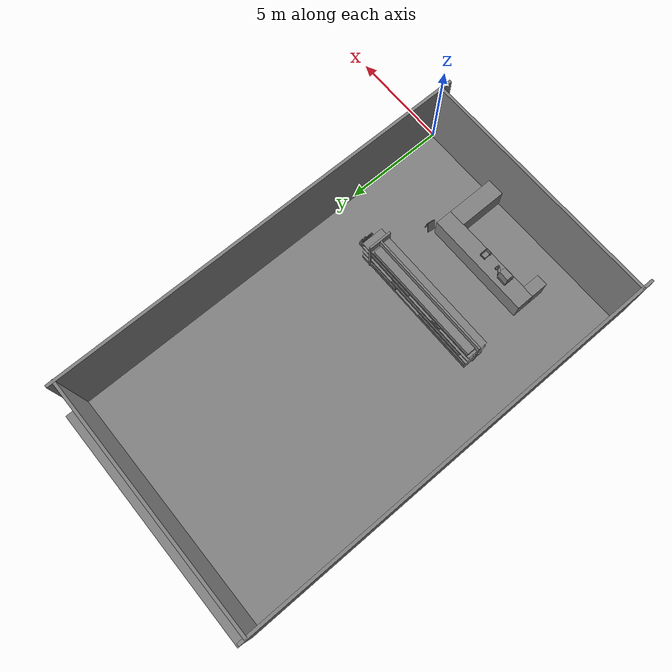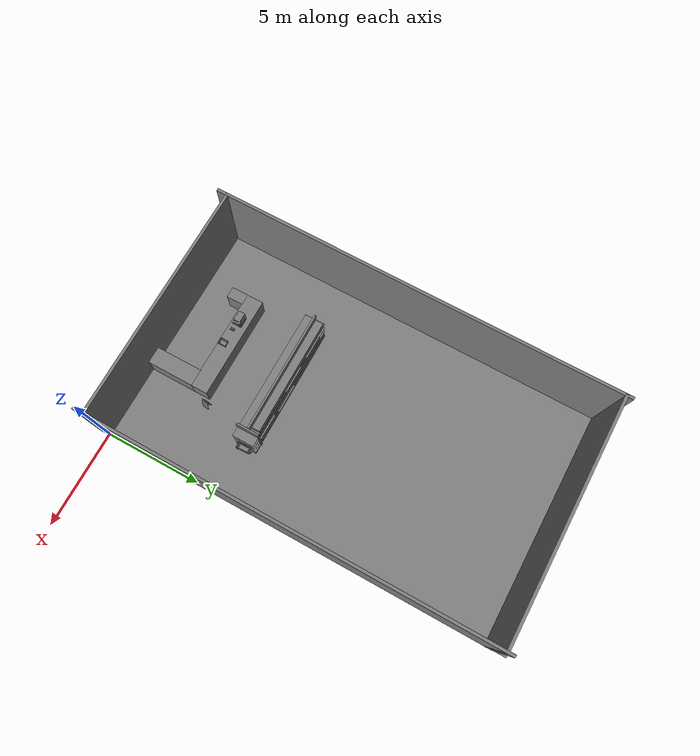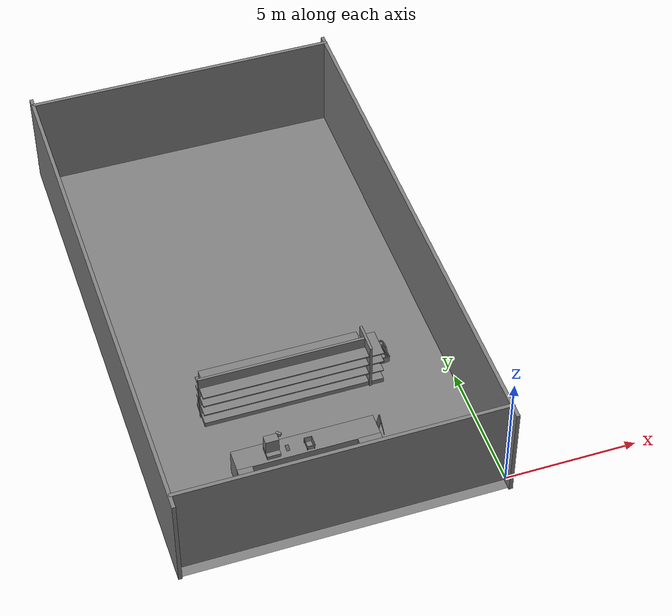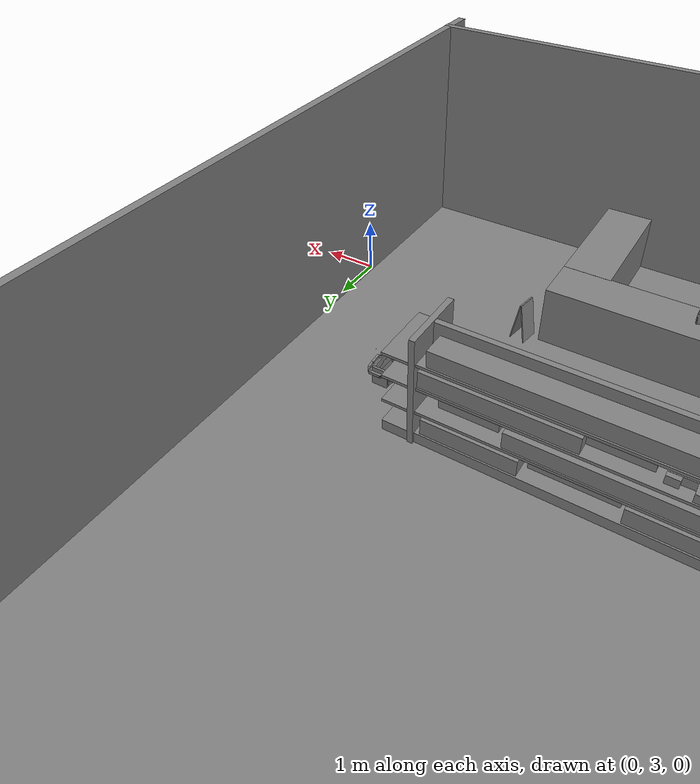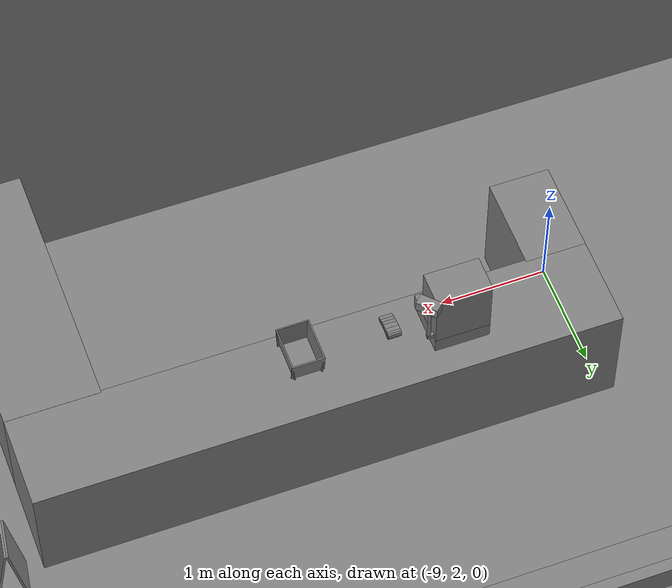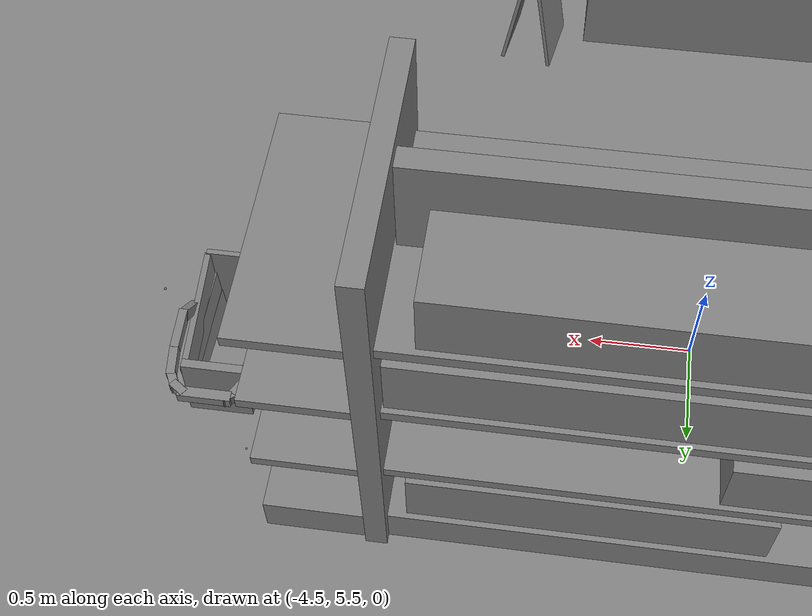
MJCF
<mujoco>
    <option gravity="0.000000000 0.000000000 -9.810000420" timestep="0.0166666" integrator="implicitfast" density="1.225" viscosity="1.8000001e-05" noslip_iterations="10" iterations="100" sdf_iterations="50">
        <flag multiccd="disable"/>
    </option>
    <size memory="1000M"/>
    <compiler coordinate="local"/>
    <worldbody>
        <light cutoff="30" pos="0 1 1" dir="0 -1 -2"/>
        <light cutoff="30" pos="0 -1 1" dir="0 1 -2"/>
        <body pos="-2.436573029 6.404376507 0.137849092" euler="0.000000000 0.000000000 0.000000000" name="[36899784347457]_shoppingtrolley_01">
            <geom contype="1" conaffinity="1" density="1000" type="box" material="" rgba="0.500000000 0.500000000 0.500000000 1.000000000" solimp="0.899999976 0.949999988 0.001000000" friction="1.000000000 0.005000000 0.000100000" solref="0.020000000 1.000000000" margin="0" condim="3" group="0" pos="0.148195267 -0.199506566 0.782808602" quat="0.998808920 0.017156634 0.026950166 0.036880098" size="0.013499999 0.305999994 0.063000001" name="[36899784347457]_geom_FE39602C_49C8_4C84_939A_C7EA65B581EA"/>
            <geom contype="1" conaffinity="1" density="1000" type="box" material="" rgba="0.500000000 0.500000000 0.500000000 1.000000000" solimp="0.899999976 0.949999988 0.001000000" friction="1.000000000 0.005000000 0.000100000" solref="0.020000000 1.000000000" margin="0" condim="3" group="0" pos="-0.000005364 0.100332208 0.734785020" quat="0.999668717 0.025737956 -0.000000010 0.000000000" size="0.135000005 0.019800000 0.152999997" name="[36899784347457]_geom_230FC44D_5ED2_41E3_B24A_9368715AAB87"/>
            <geom contype="1" conaffinity="1" density="1000" type="box" material="" rgba="0.500000000 0.500000000 0.500000000 1.000000000" solimp="0.899999976 0.949999988 0.001000000" friction="1.000000000 0.005000000 0.000100000" solref="0.020000000 1.000000000" margin="0" condim="3" group="0" pos="-0.169898406 -0.043119621 0.915120542" quat="0.687021017 0.726584017 -0.005590606 -0.006832919" size="0.017999999 0.022499999 0.089999996" name="[36899784347457]_geom_C0B7E802_42AC_43F7_BEA4_53927D939CE1"/>
            <geom contype="1" conaffinity="1" density="1000" type="box" material="" rgba="0.500000000 0.500000000 0.500000000 1.000000000" solimp="0.899999976 0.949999988 0.001000000" friction="1.000000000 0.005000000 0.000100000" solref="0.020000000 1.000000000" margin="0" condim="3" group="0" pos="-0.169898406 -0.178061336 0.864131629" quat="0.916343808 -0.400392294 -0.000000045 0.000000030" size="0.017999999 0.022499999 0.089999996" name="[36899784347457]_geom_78C3988A_A3EC_4D3B_83A6_AF70D3B09707"/>
            <geom contype="1" conaffinity="1" density="1000" type="box" material="" rgba="0.500000000 0.500000000 0.500000000 1.000000000" solimp="0.899999976 0.949999988 0.001000000" friction="1.000000000 0.005000000 0.000100000" solref="0.020000000 1.000000000" margin="0" condim="3" group="0" pos="0.103667587 0.233050480 0.912927270" quat="0.634205043 -0.622199059 -0.324503720 0.324576139" size="0.017999999 0.022499999 0.035999998" name="[36899784347457]_geom_8017601A_A409_4149_A31A_720E09E1F041"/>
            <geom contype="1" conaffinity="1" density="1000" type="box" material="" rgba="0.500000000 0.500000000 0.500000000 1.000000000" solimp="0.899999976 0.949999988 0.001000000" friction="1.000000000 0.005000000 0.000100000" solref="0.020000000 1.000000000" margin="0" condim="3" group="0" pos="0.169898629 -0.178061336 0.864131629" quat="0.916343808 -0.400392294 -0.000000045 0.000000030" size="0.017999999 0.022499999 0.089999996" name="[36899784347457]_geom_4719DA38_E2CE_4A4B_91F2_3A9F8429E888"/>
            <geom contype="1" conaffinity="1" density="1000" type="box" material="" rgba="0.500000000 0.500000000 0.500000000 1.000000000" solimp="0.899999976 0.949999988 0.001000000" friction="1.000000000 0.005000000 0.000100000" solref="0.020000000 1.000000000" margin="0" condim="3" group="0" pos="0.169898629 -0.043119621 0.915120542" quat="0.687029123 -0.726576388 -0.006509603 0.005963952" size="0.017999999 0.022499999 0.089999996" name="[36899784347457]_geom_E77F9101_07D8_44BB_A8E2_FFE12D301389"/>
            <geom contype="1" conaffinity="1" density="1000" type="box" material="" rgba="0.500000000 0.500000000 0.500000000 1.000000000" solimp="0.899999976 0.949999988 0.001000000" friction="1.000000000 0.005000000 0.000100000" solref="0.020000000 1.000000000" margin="0" condim="3" group="0" pos="-0.005004787 0.248085022 0.912686050" quat="1.000000000 0.000000000 0.000000000 0.000000000" size="0.107999995 0.022499999 0.022499999" name="[36899784347457]_geom_71E6CE70_30D7_451A_B881_5B57AF78CA87"/>
            <geom contype="1" conaffinity="1" density="1000" type="box" material="" rgba="0.500000000 0.500000000 0.500000000 1.000000000" solimp="0.899999976 0.949999988 0.001000000" friction="1.000000000 0.005000000 0.000100000" solref="0.020000000 1.000000000" margin="0" condim="3" group="0" pos="-0.000004721 -0.174527690 0.560063601" quat="0.996704638 0.081116498 -0.000000004 0.000000000" size="0.126000002 0.287999988 0.009000000" name="[36899784347457]_geom_FA75208A_17E7_4336_9AE0_B8E1769E1DBA"/>
            <geom contype="1" conaffinity="1" density="1000" type="box" material="" rgba="0.500000000 0.500000000 0.500000000 1.000000000" solimp="0.899999976 0.949999988 0.001000000" friction="1.000000000 0.005000000 0.000100000" solref="0.020000000 1.000000000" margin="0" condim="3" group="0" pos="0.134013891 0.200098798 0.912192523" quat="0.692574680 -0.680924535 -0.166899428 0.169783980" size="0.017999999 0.022499999 0.035999998" name="[36899784347457]_geom_C6181B33_A38B_4BCA_A2A3_01BB122D95C8"/>
            <geom contype="1" conaffinity="1" density="1000" type="box" material="" rgba="0.500000000 0.500000000 0.500000000 1.000000000" solimp="0.899999976 0.949999988 0.001000000" friction="1.000000000 0.005000000 0.000100000" solref="0.020000000 1.000000000" margin="0" condim="3" group="0" pos="-0.135714188 -0.191051379 0.694841146" quat="0.997147322 0.056064609 -0.045779683 -0.021407485" size="0.013499999 0.287999988 0.053999998" name="[36899784347457]_geom_97341518_8497_4D8E_977D_EC3BB01D68E8"/>
            <geom contype="1" conaffinity="1" density="1000" type="box" material="" rgba="0.500000000 0.500000000 0.500000000 1.000000000" solimp="0.899999976 0.949999988 0.001000000" friction="1.000000000 0.005000000 0.000100000" solref="0.020000000 1.000000000" margin="0" condim="3" group="0" pos="0.141839072 -0.191051379 0.702451229" quat="0.997147262 0.056065105 0.045779929 0.021407485" size="0.013499999 0.287999988 0.053999998" name="[36899784347457]_geom_29AD448A_8B2F_4724_80C5_183038E2AD9D"/>
            <geom contype="1" conaffinity="1" density="1000" type="box" material="" rgba="0.500000000 0.500000000 0.500000000 1.000000000" solimp="0.899999976 0.949999988 0.001000000" friction="1.000000000 0.005000000 0.000100000" solref="0.020000000 1.000000000" margin="0" condim="3" group="0" pos="-0.142927840 -0.199506134 0.784674108" quat="0.998421252 0.016904408 -0.027109101 -0.046199299" size="0.013499999 0.305999994 0.063000001" name="[36899784347457]_geom_6EE2B28C_D194_4C1D_B50F_18BFB348610B"/>
            <geom contype="1" conaffinity="1" density="1000" type="box" material="" rgba="0.500000000 0.500000000 0.500000000 1.000000000" solimp="0.899999976 0.949999988 0.001000000" friction="1.000000000 0.005000000 0.000100000" solref="0.020000000 1.000000000" margin="0" condim="3" group="0" pos="-0.000006008 -0.484932661 0.670727849" quat="0.997585475 0.069449045 -0.000000004 -0.000000089" size="0.179999992 0.013499999 0.170999989" name="[36899784347457]_geom_2C0BC05A_9856_4B2A_B762_EB442C43A2AC"/>
            <geom contype="1" conaffinity="1" density="1000" type="box" material="" rgba="0.500000000 0.500000000 0.500000000 1.000000000" solimp="0.899999976 0.949999988 0.001000000" friction="1.000000000 0.005000000 0.000100000" solref="0.020000000 1.000000000" margin="0" condim="3" group="0" pos="-0.160832763 0.103427693 0.910528183" quat="0.711469591 0.699786782 -0.048386075 -0.042050660" size="0.017999999 0.022499999 0.071999997" name="[36899784347457]_geom_AE5EAD67_9B20_4953_8FE7_ECB6632C43CE"/>
            <geom contype="1" conaffinity="1" density="1000" type="box" material="" rgba="0.500000000 0.500000000 0.500000000 1.000000000" solimp="0.899999976 0.949999988 0.001000000" friction="1.000000000 0.005000000 0.000100000" solref="0.020000000 1.000000000" margin="0" condim="3" group="0" pos="0.131482959 -0.182533979 0.598989725" quat="0.996607125 0.055331629 0.059003670 0.015205893" size="0.013499999 0.287999988 0.053999998" name="[36899784347457]_geom_A3A0D09B_8187_4AC9_8FD3_5B4105858AB7"/>
            <geom contype="1" conaffinity="1" density="1000" type="box" material="" rgba="0.500000000 0.500000000 0.500000000 1.000000000" solimp="0.899999976 0.949999988 0.001000000" friction="1.000000000 0.005000000 0.000100000" solref="0.020000000 1.000000000" margin="0" condim="3" group="0" pos="-0.134013891 0.200098798 0.912192523" quat="0.694057047 0.679413557 -0.172947660 -0.163618833" size="0.017999999 0.022499999 0.035999998" name="[36899784347457]_geom_9E71ED22_1C35_43AA_BE03_72658B49DCA5"/>
            <geom contype="1" conaffinity="1" density="1000" type="box" material="" rgba="0.500000000 0.500000000 0.500000000 1.000000000" solimp="0.899999976 0.949999988 0.001000000" friction="1.000000000 0.005000000 0.000100000" solref="0.020000000 1.000000000" margin="0" condim="3" group="0" pos="-0.126757339 -0.182533979 0.598989725" quat="0.996607184 0.055331606 -0.059003651 -0.015205891" size="0.013499999 0.287999988 0.053999998" name="[36899784347457]_geom_C08EEAE3_5D93_4765_B57A_6065A2C314B4"/>
            <geom contype="1" conaffinity="1" density="1000" type="box" material="" rgba="0.500000000 0.500000000 0.500000000 1.000000000" solimp="0.899999976 0.949999988 0.001000000" friction="1.000000000 0.005000000 0.000100000" solref="0.020000000 1.000000000" margin="0" condim="3" group="0" pos="-0.107458733 0.238907143 0.911498845" quat="0.634576976 0.622505128 -0.330067992 -0.317575932" size="0.017999999 0.022499999 0.035999998" name="[36899784347457]_geom_79E1F97A_CE63_44F2_9CFC_E509C9E01393"/>
            <geom contype="1" conaffinity="1" density="1000" type="box" material="" rgba="0.500000000 0.500000000 0.500000000 1.000000000" solimp="0.899999976 0.949999988 0.001000000" friction="1.000000000 0.005000000 0.000100000" solref="0.020000000 1.000000000" margin="0" condim="3" group="0" pos="0.160832971 0.103427693 0.910528183" quat="0.711112797 -0.700149298 -0.042821646 0.047705106" size="0.017999999 0.022499999 0.071999997" name="[36899784347457]_geom_0D83B2F9_78DD_4BE7_B70A_00B4ED22CCE3"/>
            <site size="0.005000000 0.005000000 0.005000000" rgba="0.500000000 0.500000000 0.500000000 1.000000000" pos="0.000000000 0.000000000 0.000000000" quat="1.000000000 0.000000000 0.000000000 0.000000000" group="0" type="sphere" name="[36899784347457]_shoppingtrolley_01"/>
        </body>
        <body pos="-7.168000221 2.823999882 1.227496982" euler="-0.283413887 0.056829713 -0.133293241" name="openloong_gripper_2f85_fix_base_usda_Pos">
            <geom contype="1" conaffinity="1" density="1000" type="box" material="" rgba="0.500000000 0.500000000 0.500000000 1.000000000" solimp="0.899999976 0.949999988 0.001000000" friction="1.000000000 0.005000000 0.000100000" solref="0.020000000 1.000000000" margin="0" condim="3" group="0" pos="-0.002278805 0.074524641 -0.004134178" quat="0.315989256 0.948762834 0.000000000 0.000000000" size="0.059999999 0.013000000 0.035000000" name="openloong_gripper_2f85_fix_base_usda_geom_4A5DB32D_3C0C_41DE_A493_DD0EC00F46E1"/>
            <geom contype="1" conaffinity="1" density="1000" type="box" material="" rgba="0.500000000 0.500000000 0.500000000 1.000000000" solimp="0.899999976 0.949999988 0.001000000" friction="1.000000000 0.005000000 0.000100000" solref="0.020000000 1.000000000" margin="0" condim="3" group="0" pos="-0.002278805 0.078031301 0.008128285" quat="0.990447283 -0.137893349 -0.000000000 0.000000000" size="0.059999999 0.010000000 0.035000000" name="openloong_gripper_2f85_fix_base_usda_geom_499BAC20_CD24_4929_9104_A3971E460943"/>
            <geom contype="1" conaffinity="1" density="1000" type="box" material="" rgba="0.500000000 0.500000000 0.500000000 1.000000000" solimp="0.899999976 0.949999988 0.001000000" friction="1.000000000 0.005000000 0.000100000" solref="0.020000000 1.000000000" margin="0" condim="3" group="0" pos="-0.002278805 0.080785275 -0.002596974" quat="0.287325412 -0.957833171 0.000000000 -0.000000000" size="0.059999999 0.013000000 0.035000000" name="openloong_gripper_2f85_fix_base_usda_geom_0464C5A0_D9F2_45CC_86B2_4C2E52C55CCC"/>
            <geom contype="1" conaffinity="1" density="1000" type="box" material="" rgba="0.500000000 0.500000000 0.500000000 1.000000000" solimp="0.899999976 0.949999988 0.001000000" friction="1.000000000 0.005000000 0.000100000" solref="0.020000000 1.000000000" margin="0" condim="3" group="0" pos="-0.002278805 -0.098804474 -0.020147085" quat="0.988851428 0.148906425 0.000000000 -0.000000000" size="0.059999999 0.022000000 0.020000000" name="openloong_gripper_2f85_fix_base_usda_geom_F0AA9742_59C8_4767_BC09_85C1BF5A72F6"/>
            <geom contype="1" conaffinity="1" density="1000" type="box" material="" rgba="0.500000000 0.500000000 0.500000000 1.000000000" solimp="0.899999976 0.949999988 0.001000000" friction="1.000000000 0.005000000 0.000100000" solref="0.020000000 1.000000000" margin="0" condim="3" group="0" pos="-0.002279282 0.019920349 0.012102842" quat="0.995421529 0.095583312 -0.000000000 0.000000000" size="0.059999999 0.025000000 0.026000001" name="openloong_gripper_2f85_fix_base_usda_geom_27F13DA8_E85C_47C1_9B39_B538FEDBE2FB"/>
            <geom contype="1" conaffinity="1" density="1000" type="box" material="" rgba="0.500000000 0.500000000 0.500000000 1.000000000" solimp="0.899999976 0.949999988 0.001000000" friction="1.000000000 0.005000000 0.000100000" solref="0.020000000 1.000000000" margin="0" condim="3" group="0" pos="-0.002279282 0.005734444 -0.014276981" quat="0.999571502 -0.029275293 -0.000000000 0.000000000" size="0.059999999 0.050000001 0.010000000" name="openloong_gripper_2f85_fix_base_usda_geom_E4FF863D_FC68_4AE6_A5F7_DCA80128840E"/>
            <geom contype="1" conaffinity="1" density="1000" type="box" material="" rgba="0.500000000 0.500000000 0.500000000 1.000000000" solimp="0.899999976 0.949999988 0.001000000" friction="1.000000000 0.005000000 0.000100000" solref="0.020000000 1.000000000" margin="0" condim="3" group="0" pos="-0.002278805 0.079460382 0.007771969" quat="0.922590315 -0.385781497 -0.000000000 0.000000000" size="0.059999999 0.010000000 0.035000000" name="openloong_gripper_2f85_fix_base_usda_geom_9C348893_212F_4E73_99CD_FD6E22E12EEA"/>
            <geom contype="1" conaffinity="1" density="1000" type="box" material="" rgba="0.500000000 0.500000000 0.500000000 1.000000000" solimp="0.899999976 0.949999988 0.001000000" friction="1.000000000 0.005000000 0.000100000" solref="0.020000000 1.000000000" margin="0" condim="3" group="0" pos="-0.002279282 0.081384182 -0.001320124" quat="0.590483606 -0.807049692 0.000000000 0.000000000" size="0.059999999 0.013000000 0.035000000" name="openloong_gripper_2f85_fix_base_usda_geom_EB7C8844_B3A5_41D7_B2A0_B12DDDB8E805"/>
            <geom contype="1" conaffinity="1" density="1000" type="box" material="" rgba="0.500000000 0.500000000 0.500000000 1.000000000" solimp="0.899999976 0.949999988 0.001000000" friction="1.000000000 0.005000000 0.000100000" solref="0.020000000 1.000000000" margin="0" condim="3" group="0" pos="-0.002278805 -0.059297562 -0.007972836" quat="0.988851428 0.148906425 0.000000000 -0.000000000" size="0.059999999 0.020000000 0.022000000" name="openloong_gripper_2f85_fix_base_usda_geom_A0FD2700_17D1_41CF_A2BD_8693B300E4DD"/>
            <geom contype="1" conaffinity="1" density="1000" type="box" material="" rgba="0.500000000 0.500000000 0.500000000 1.000000000" solimp="0.899999976 0.949999988 0.001000000" friction="1.000000000 0.005000000 0.000100000" solref="0.020000000 1.000000000" margin="0" condim="3" group="0" pos="-0.002278805 0.076618671 -0.004656911" quat="0.004634960 0.999989390 -0.000000000 0.000000000" size="0.059999999 0.013000000 0.035000000" name="openloong_gripper_2f85_fix_base_usda_geom_F6A1EEAC_DEA4_43C1_ADDA_F1D080B464AA"/>
            <geom contype="1" conaffinity="1" density="1000" type="box" material="" rgba="0.500000000 0.500000000 0.500000000 1.000000000" solimp="0.899999976 0.949999988 0.001000000" friction="1.000000000 0.005000000 0.000100000" solref="0.020000000 1.000000000" margin="0" condim="3" group="0" pos="-0.002279282 -0.021952629 0.002959967" quat="0.991270185 0.131847635 0.000000000 -0.000000000" size="0.059999999 0.020000000 0.024000000" name="openloong_gripper_2f85_fix_base_usda_geom_414FFC6F_45F6_4C83_90FB_47F7FB1AFA3D"/>
            <geom contype="1" conaffinity="1" density="1000" type="box" material="" rgba="0.500000000 0.500000000 0.500000000 1.000000000" solimp="0.899999976 0.949999988 0.001000000" friction="1.000000000 0.005000000 0.000100000" solref="0.020000000 1.000000000" margin="0" condim="3" group="0" pos="-0.002278805 0.081418991 0.002587795" quat="0.803492188 -0.595315576 0.000000000 0.000000000" size="0.059999999 0.013000000 0.035000000" name="openloong_gripper_2f85_fix_base_usda_geom_DA162E1F_7227_4C77_8926_CCDEA51EE4B8"/>
            <geom contype="1" conaffinity="1" density="1000" type="box" material="" rgba="0.500000000 0.500000000 0.500000000 1.000000000" solimp="0.899999976 0.949999988 0.001000000" friction="1.000000000 0.005000000 0.000100000" solref="0.020000000 1.000000000" margin="0" condim="3" group="0" pos="-0.002278805 0.061115503 0.008545756" quat="0.999325931 0.036714435 -0.000000000 -0.000000000" size="0.059999999 0.020000000 0.035000000" name="openloong_gripper_2f85_fix_base_usda_geom_76CFCD8F_D2BD_4939_8A15_DD6D10228690"/>
            <freejoint name="openloong_gripper_2f85_fix_base_usda_pos_scan"/>
        </body>
        <body pos="-6.332345009 2.779978037 1.034067392" euler="0.000000000 0.000000000 0.000000000" name="openloong_gripper_2f85_fix_base_usda_basket">
            <geom contype="1" conaffinity="1" density="100000" type="box" material="" rgba="0.500000000 0.500000000 0.500000000 1.000000000" solimp="0.899999976 0.949999988 0.001000000" friction="1.000000000 0.899999976 0.000100000" solref="0.020000000 1.000000000" margin="0" condim="3" group="0" pos="-0.172339439 0.000000000 0.168361664" quat="0.706172407 -0.036353018 -0.036353093 0.706170976" size="0.200000003 0.006000000 0.108000003" name="openloong_gripper_2f85_fix_base_usda_geom_5398B64E_3684_4E2B_93AD_5BBA749A1CAD"/>
            <geom contype="1" conaffinity="1" density="100000" type="box" material="" rgba="0.500000000 0.500000000 0.500000000 1.000000000" solimp="0.899999976 0.949999988 0.001000000" friction="1.000000000 0.899999976 0.000100000" solref="0.020000000 1.000000000" margin="0" condim="3" group="0" pos="-0.039724827 -0.188568115 0.167089701" quat="0.997537494 0.070135131 0.000000000 0.000000000" size="0.150000006 0.006000000 0.108000003" name="openloong_gripper_2f85_fix_base_usda_geom_C14B5FA0_0B4B_4408_845E_59F768A852C2"/>
            <geom contype="1" conaffinity="1" density="100000" type="box" material="" rgba="0.500000000 0.500000000 0.500000000 1.000000000" solimp="0.899999976 0.949999988 0.001000000" friction="1.000000000 0.899999976 0.000100000" solref="0.020000000 1.000000000" margin="0" condim="3" group="0" pos="-0.039724827 0.188377380 0.167089701" quat="0.997489929 -0.070808925 0.000000000 0.000000000" size="0.150000006 0.006000000 0.108000003" name="openloong_gripper_2f85_fix_base_usda_geom_8A63D6EA_2C8C_44AD_BF09_99C8A6B404D3"/>
            <geom contype="1" conaffinity="1" density="100000" type="box" material="" rgba="0.500000000 0.500000000 0.500000000 1.000000000" solimp="0.899999976 0.949999988 0.001000000" friction="1.000000000 0.899999976 0.000100000" solref="0.020000000 1.000000000" margin="0" condim="3" group="0" pos="-0.039724827 0.000000000 0.068126202" quat="1.000000000 0.000000000 0.000000000 0.000000000" size="0.129999995 0.174999997 0.006000000" name="openloong_gripper_2f85_fix_base_usda_geom_0FE6F675_5367_49FC_877E_DCDE8DC4AE7E"/>
            <geom contype="1" conaffinity="1" density="100000" type="box" material="" rgba="0.500000000 0.500000000 0.500000000 1.000000000" solimp="0.899999976 0.949999988 0.001000000" friction="1.000000000 0.899999976 0.000100000" solref="0.020000000 1.000000000" margin="0" condim="3" group="0" pos="0.094372749 0.000000000 0.168361664" quat="0.706172049 0.036353335 0.036353379 0.706171215" size="0.200000003 0.006000000 0.108000003" name="openloong_gripper_2f85_fix_base_usda_geom_5067D883_369F_4817_8EA2_5D80230CF593"/>
            <freejoint name="openloong_gripper_2f85_fix_base_usda_basket_joint"/>
            <site size="0.005000000 0.005000000 0.005000000" rgba="0.500000000 0.500000000 0.500000000 1.000000000" pos="0.000000000 0.000000000 0.000000000" quat="1.000000000 0.000000000 0.000000000 0.000000000" group="0" type="sphere" name="openloong_gripper_2f85_fix_base_usda_basketsite"/>
        </body>
        <body pos="-3.510578632 3.403555870 -0.000000100" euler="0.000000000 0.000000000 40.200675964" name="openloong_gripper_2f85_fix_base_usda_PZ">
            <geom contype="1" conaffinity="1" density="1000" type="box" material="" rgba="0.500000000 0.500000000 0.500000000 1.000000000" solimp="0.899999976 0.949999988 0.001000000" friction="1.000000000 0.005000000 0.000100000" solref="0.020000000 1.000000000" margin="0" condim="3" group="0" pos="-0.047453165 0.056484699 0.373715430" quat="0.934750080 0.077914521 0.028795123 0.345459938" size="0.180000007 0.010000000 0.379999995" name="openloong_gripper_2f85_fix_base_usda_geom_70B48A1B_9F74_421B_A04E_E711F7EAAF7A"/>
            <geom contype="1" conaffinity="1" density="1000" type="box" material="" rgba="0.500000000 0.500000000 0.500000000 1.000000000" solimp="0.899999976 0.949999988 0.001000000" friction="1.000000000 0.005000000 0.000100000" solref="0.020000000 1.000000000" margin="0" condim="3" group="0" pos="0.047452450 -0.054376602 0.374072611" quat="0.934387863 -0.082143910 -0.030358355 0.345326364" size="0.180000007 0.010000000 0.379999995" name="openloong_gripper_2f85_fix_base_usda_geom_A567BF41_965C_4B93_89C0_3B40CA118650"/>
            <freejoint name="openloong_gripper_2f85_fix_base_usda_PZ"/>
        </body>
        <body pos="0.000000000 0.000000000 0.000000000" euler="0.000000000 0.000000000 0.000000000" name="Interactive Objects_Interactive Objects"/>
        <body pos="0.000000000 0.000000000 0.000000000" euler="0.000000000 0.000000000 0.000000000" name=" Static Objects_ Static Objects">
            <geom contype="1" conaffinity="1" density="1000" type="box" material="" rgba="0.500000000 0.500000000 0.500000000 1.000000000" solimp="0.899999976 0.949999988 0.001000000" friction="1.000000000 0.005000000 0.000100000" solref="0.020000000 1.000000000" margin="0" condim="3" group="0" pos="-3.101639986 6.150595188 1.018643856" quat="1.000000000 0.000000000 0.000000000 0.000000000" size="0.050000001 0.579999983 1.019999981" name=" Static Objects_geom_28F97954_2BF1_40FB_A754_F9A30AAF42B8"/>
            <geom contype="1" conaffinity="1" density="1000" type="box" material="" rgba="0.500000000 0.500000000 0.500000000 1.000000000" solimp="0.899999976 0.949999988 0.001000000" friction="1.000000000 0.005000000 0.000100000" solref="0.020000000 1.000000000" margin="0" condim="3" group="0" pos="-2.825197220 6.153595448 1.115278244" quat="0.707107067 0.000000000 0.000000000 0.707106471" size="0.550000012 0.239999995 0.025000000" name=" Static Objects_geom_0C8B9853_3567_49CA_8220_3A0AA4B6EAEF"/>
            <geom contype="1" conaffinity="1" density="1000" type="box" material="" rgba="0.500000000 0.500000000 0.500000000 1.000000000" solimp="0.899999976 0.949999988 0.001000000" friction="1.000000000 0.005000000 0.000100000" solref="0.020000000 1.000000000" margin="0" condim="3" group="0" pos="-2.825197220 6.153595448 0.097434282" quat="0.707107067 0.000000000 0.000000000 0.707106471" size="0.550000012 0.239999995 0.098999999" name=" Static Objects_geom_DA56A36F_23D3_4E70_BEAA_D2FC4C6869AB"/>
            <geom contype="1" conaffinity="1" density="1000" type="box" material="" rgba="0.500000000 0.500000000 0.500000000 1.000000000" solimp="0.899999976 0.949999988 0.001000000" friction="1.000000000 0.005000000 0.000100000" solref="0.020000000 1.000000000" margin="0" condim="3" group="0" pos="-6.293097973 6.153595448 1.114443064" quat="0.707107067 0.000000000 0.000000000 0.707106471" size="0.529999971 3.134999990 0.025000000" name=" Static Objects_geom_DFCD37BC_BBC7_4DDA_A96D_22786CE28451"/>
            <geom contype="1" conaffinity="1" density="1000" type="box" material="" rgba="0.500000000 0.500000000 0.500000000 1.000000000" solimp="0.899999976 0.949999988 0.001000000" friction="1.000000000 0.005000000 0.000100000" solref="0.020000000 1.000000000" margin="0" condim="3" group="0" pos="-2.825197220 6.153595448 1.563861728" quat="0.707107067 0.000000000 0.000000000 0.707106471" size="0.550000012 0.239999995 0.025000000" name=" Static Objects_geom_13148A73_F8E2_44CA_BEB7_B8236C130946"/>
            <geom contype="1" conaffinity="1" density="1000" type="box" material="" rgba="0.500000000 0.500000000 0.500000000 1.000000000" solimp="0.899999976 0.949999988 0.001000000" friction="1.000000000 0.005000000 0.000100000" solref="0.020000000 1.000000000" margin="0" condim="3" group="0" pos="-6.311686516 6.153595448 1.018643856" quat="0.707107067 0.000000000 0.000000000 0.707106471" size="0.050000001 3.150000095 1.019999981" name=" Static Objects_geom_CE3B01EE_D494_4924_89B6_A3AD48F9E0E3"/>
            <geom contype="1" conaffinity="1" density="1000" type="box" material="" rgba="0.500000000 0.500000000 0.500000000 1.000000000" solimp="0.899999976 0.949999988 0.001000000" friction="1.000000000 0.005000000 0.000100000" solref="0.020000000 1.000000000" margin="0" condim="3" group="0" pos="-6.286010742 6.153595448 0.096129179" quat="0.707107067 0.000000000 0.000000000 0.707106471" size="0.529999971 3.134999990 0.098999999" name=" Static Objects_geom_332B04BD_0357_4CC5_9105_5B19A352F63C"/>
            <geom contype="1" conaffinity="1" density="1000" type="box" material="" rgba="0.500000000 0.500000000 0.500000000 1.000000000" solimp="0.899999976 0.949999988 0.001000000" friction="1.000000000 0.005000000 0.000100000" solref="0.020000000 1.000000000" margin="0" condim="3" group="0" pos="-2.825197220 6.153595448 0.629031777" quat="0.707107067 0.000000000 0.000000000 0.707106471" size="0.550000012 0.239999995 0.025000000" name=" Static Objects_geom_F6B9FAFC_D828_4D4A_BDF1_18E581EFDC05"/>
            <geom contype="1" conaffinity="1" density="1000" type="box" material="" rgba="0.500000000 0.500000000 0.500000000 1.000000000" solimp="0.899999976 0.949999988 0.001000000" friction="1.000000000 0.005000000 0.000100000" solref="0.020000000 1.000000000" margin="0" condim="3" group="0" pos="-6.286010742 6.153595448 1.563861728" quat="0.707107067 0.000000000 0.000000000 0.707106471" size="0.529999971 3.134999990 0.025000000" name=" Static Objects_geom_B628C79F_2EB1_4CD2_8977_9D02769F1F90"/>
            <geom contype="1" conaffinity="1" density="1000" type="box" material="" rgba="0.500000000 0.500000000 0.500000000 1.000000000" solimp="0.899999976 0.949999988 0.001000000" friction="1.000000000 0.005000000 0.000100000" solref="0.020000000 1.000000000" margin="0" condim="3" group="0" pos="-6.286010742 6.153595448 0.629031777" quat="0.707107067 0.000000000 0.000000000 0.707106471" size="0.529999971 3.134999990 0.025000000" name=" Static Objects_geom_67F575B2_49E9_4533_A15B_9B58C0DF80DE"/>
            <geom contype="1" conaffinity="1" density="1000" type="box" material="" rgba="0.500000000 0.500000000 0.500000000 1.000000000" solimp="0.899999976 0.949999988 0.001000000" friction="1.000000000 0.005000000 0.000100000" solref="0.020000000 1.000000000" margin="0" condim="3" group="0" pos="-7.719123363 2.867671013 1.173410416" quat="1.000000000 0.000000000 0.000000000 0.000000000" size="0.250000000 0.250000000 0.079999998" name=" Static Objects_geom_0395B330_AE7A_41A6_8464_74E76AF306E8"/>
            <geom contype="1" conaffinity="1" density="1000" type="box" material="" rgba="0.500000000 0.500000000 0.500000000 1.000000000" solimp="0.899999976 0.949999988 0.001000000" friction="1.000000000 0.005000000 0.000100000" solref="0.020000000 1.000000000" margin="0" condim="3" group="0" pos="-7.408766270 3.088089943 1.776644945" quat="0.928051054 0.000000000 0.000000000 0.372453064" size="0.050000001 0.100000001 0.050000001" name=" Static Objects_geom_8A5AAB8C_A324_4538_863F_1082D3B26C1B"/>
            <geom contype="1" conaffinity="1" density="1000" type="box" material="" rgba="0.500000000 0.500000000 0.500000000 1.000000000" solimp="0.899999976 0.949999988 0.001000000" friction="1.000000000 0.005000000 0.000100000" solref="0.020000000 1.000000000" margin="0" condim="3" group="0" pos="-7.719123363 2.958004713 1.530241251" quat="1.000000000 0.000000000 0.000000000 0.000000000" size="0.250000000 0.159999996 0.280000001" name=" Static Objects_geom_CACDBE30_175F_49F8_8B1F_6AD6783D50BA"/>
            <geom contype="1" conaffinity="1" density="1000" type="cylinder" material="" rgba="0.500000000 0.500000000 0.500000000 1.000000000" solimp="0.899999976 0.949999988 0.001000000" friction="1.000000000 0.005000000 0.000100000" solref="0.020000000 1.000000000" margin="0" condim="3" group="0" pos="-7.427312374 3.069516420 1.502544641" quat="0.928051054 0.000000000 0.000000000 0.372453064" size="0.015000000 0.230000004 0.100000001" name=" Static Objects_geom_222562B4_C0E7_4F87_A877_7EBFE98CD493"/>
            <geom contype="1" conaffinity="1" density="1000" type="box" material="" rgba="0.500000000 0.500000000 0.500000000 1.000000000" solimp="0.899999976 0.949999988 0.001000000" friction="1.000000000 0.005000000 0.000100000" solref="0.020000000 1.000000000" margin="0" condim="3" group="0" pos="-7.437745571 3.067511320 1.289965630" quat="1.000000000 0.000000000 0.000000000 0.000000000" size="0.029999999 0.020000000 0.020000000" name=" Static Objects_geom_415BCEC4_1353_43C0_9F23_FCA9A42DF799"/>
            <geom contype="1" conaffinity="1" density="1000" type="box" material="" rgba="0.500000000 0.500000000 0.500000000 1.000000000" solimp="0.899999976 0.949999988 0.001000000" friction="1.000000000 0.005000000 0.000100000" solref="0.020000000 1.000000000" margin="0" condim="3" group="0" pos="-9.058088303 6.434794426 1.209077358" quat="1.000000000 0.000000000 0.000000000 0.000000000" size="0.250000000 0.100000001 0.070000000" name=" Static Objects_geom_4C0D8DD6_C635_4026_A744_1AA8A2903909"/>
            <geom contype="1" conaffinity="1" density="1000" type="box" material="" rgba="0.500000000 0.500000000 0.500000000 1.000000000" solimp="0.899999976 0.949999988 0.001000000" friction="1.000000000 0.005000000 0.000100000" solref="0.020000000 1.000000000" margin="0" condim="3" group="0" pos="-7.886891365 6.459744930 0.352518857" quat="1.000000000 0.000000000 0.000000000 0.000000000" size="1.500000000 0.200000003 0.150000006" name=" Static Objects_geom_65D70240_BA53_478B_A3D4_DA8C87BC3FFF"/>
            <geom contype="1" conaffinity="1" density="1000" type="box" material="" rgba="0.500000000 0.500000000 0.500000000 1.000000000" solimp="0.899999976 0.949999988 0.001000000" friction="1.000000000 0.005000000 0.000100000" solref="0.020000000 1.000000000" margin="0" condim="3" group="0" pos="-9.237723351 6.464855671 1.209077358" quat="1.000000000 0.000000000 0.000000000 0.000000000" size="0.100000001 0.100000001 0.070000000" name=" Static Objects_geom_237DAE2A_7A0C_4B12_94C6_F61CA147A26A"/>
            <geom contype="1" conaffinity="1" density="1000" type="box" material="" rgba="0.500000000 0.500000000 0.500000000 1.000000000" solimp="0.899999976 0.949999988 0.001000000" friction="1.000000000 0.005000000 0.000100000" solref="0.020000000 1.000000000" margin="0" condim="3" group="0" pos="-6.924745083 6.362090111 1.214329123" quat="1.000000000 0.000000000 0.000000000 0.000000000" size="0.200000003 0.100000001 0.075000003" name=" Static Objects_geom_2FB2F8DE_5F5E_4A97_A24C_4A484CDE4612"/>
            <geom contype="1" conaffinity="1" density="1000" type="box" material="" rgba="0.500000000 0.500000000 0.500000000 1.000000000" solimp="0.899999976 0.949999988 0.001000000" friction="1.000000000 0.005000000 0.000100000" solref="0.020000000 1.000000000" margin="0" condim="3" group="0" pos="-4.407354832 6.459744930 1.292199373" quat="1.000000000 0.000000000 0.000000000 0.000000000" size="1.240000010 0.200000003 0.150000006" name=" Static Objects_geom_D8EFC1FE_8C67_4AB9_8D4E_E25F48E756BE"/>
            <geom contype="1" conaffinity="1" density="1000" type="box" material="" rgba="0.500000000 0.500000000 0.500000000 1.000000000" solimp="0.899999976 0.949999988 0.001000000" friction="1.000000000 0.005000000 0.000100000" solref="0.020000000 1.000000000" margin="0" condim="3" group="0" pos="-5.611940861 6.318420410 0.350975692" quat="1.000000000 0.000000000 0.000000000 0.000000000" size="0.699999988 0.100000001 0.150000006" name=" Static Objects_geom_48DC29B4_7071_4CF2_AF39_D811C5558517"/>
            <geom contype="1" conaffinity="1" density="1000" type="box" material="" rgba="0.500000000 0.500000000 0.500000000 1.000000000" solimp="0.899999976 0.949999988 0.001000000" friction="1.000000000 0.005000000 0.000100000" solref="0.020000000 1.000000000" margin="0" condim="3" group="0" pos="-6.300771236 6.459744930 1.744376063" quat="1.000000000 0.000000000 0.000000000 0.000000000" size="3.000000000 0.200000003 0.150000006" name=" Static Objects_geom_FDE4D5CB_E9FB_425C_91B0_D1BE7C2EF0C8"/>
            <geom contype="1" conaffinity="1" density="1000" type="box" material="" rgba="0.500000000 0.500000000 0.500000000 1.000000000" solimp="0.899999976 0.949999988 0.001000000" friction="1.000000000 0.005000000 0.000100000" solref="0.020000000 1.000000000" margin="0" condim="3" group="0" pos="-8.844120979 6.464855671 1.209077358" quat="1.000000000 0.000000000 0.000000000 0.000000000" size="0.100000001 0.100000001 0.070000000" name=" Static Objects_geom_01AD7C1F_1445_4166_8BFA_A0A4D81944B8"/>
            <geom contype="1" conaffinity="1" density="1000" type="box" material="" rgba="0.500000000 0.500000000 0.500000000 1.000000000" solimp="0.899999976 0.949999988 0.001000000" friction="1.000000000 0.005000000 0.000100000" solref="0.020000000 1.000000000" margin="0" condim="3" group="0" pos="-6.824534416 6.447464466 1.212718010" quat="1.000000000 0.000000000 0.000000000 0.000000000" size="0.100000001 0.100000001 0.075000003" name=" Static Objects_geom_8B55E196_1EE4_4DE3_8D47_C47BCC3442BB"/>
            <geom contype="1" conaffinity="1" density="1000" type="box" material="" rgba="0.500000000 0.500000000 0.500000000 1.000000000" solimp="0.899999976 0.949999988 0.001000000" friction="1.000000000 0.005000000 0.000100000" solref="0.020000000 1.000000000" margin="0" condim="3" group="0" pos="-6.751636982 6.459744930 0.800981164" quat="1.000000000 0.000000000 0.000000000 0.000000000" size="2.200000048 0.200000003 0.150000006" name=" Static Objects_geom_192CDE75_420D_4D62_9FC1_3934E681A49D"/>
            <geom contype="1" conaffinity="1" density="1000" type="box" material="" rgba="0.500000000 0.500000000 0.500000000 1.000000000" solimp="0.899999976 0.949999988 0.001000000" friction="1.000000000 0.005000000 0.000100000" solref="0.020000000 1.000000000" margin="0" condim="3" group="0" pos="-6.098561764 6.327973843 1.292199373" quat="1.000000000 0.000000000 0.000000000 0.000000000" size="0.500000000 0.100000001 0.150000006" name=" Static Objects_geom_B3F0F5F9_5E7F_4351_A326_CA3A9C8D3FAC"/>
            <geom contype="1" conaffinity="1" density="1000" type="box" material="" rgba="0.500000000 0.500000000 0.500000000 1.000000000" solimp="0.899999976 0.949999988 0.001000000" friction="1.000000000 0.005000000 0.000100000" solref="0.020000000 1.000000000" margin="0" condim="3" group="0" pos="-3.907610416 6.318625927 0.800981164" quat="1.000000000 0.000000000 0.000000000 0.000000000" size="0.500000000 0.100000001 0.150000006" name=" Static Objects_geom_723923C6_37EC_4DA8_ACDA_77439A694C8F"/>
            <geom contype="1" conaffinity="1" density="1000" type="box" material="" rgba="0.500000000 0.500000000 0.500000000 1.000000000" solimp="0.899999976 0.949999988 0.001000000" friction="1.000000000 0.005000000 0.000100000" solref="0.020000000 1.000000000" margin="0" condim="3" group="0" pos="-7.373087406 6.458900928 1.214329123" quat="1.000000000 0.000000000 0.000000000 0.000000000" size="0.250000000 0.200000003 0.075000003" name=" Static Objects_geom_1235BCBF_AE00_4155_B7F7_58B2E59CC89B"/>
            <geom contype="1" conaffinity="1" density="1000" type="box" material="" rgba="0.500000000 0.500000000 0.500000000 1.000000000" solimp="0.899999976 0.949999988 0.001000000" friction="1.000000000 0.005000000 0.000100000" solref="0.020000000 1.000000000" margin="0" condim="3" group="0" pos="-4.035642624 6.459744930 0.352518857" quat="1.000000000 0.000000000 0.000000000 0.000000000" size="0.800000012 0.200000003 0.150000006" name=" Static Objects_geom_ADA99610_6A6C_4DAA_83E9_4FDBB67BC395"/>
            <geom contype="1" conaffinity="1" density="1000" type="box" material="" rgba="0.500000000 0.500000000 0.500000000 1.000000000" solimp="0.899999976 0.949999988 0.001000000" friction="1.000000000 0.005000000 0.000100000" solref="0.020000000 1.000000000" margin="0" condim="3" group="0" pos="-6.460197449 2.937205315 0.548931718" quat="1.000000000 0.000000000 0.000000000 0.000000000" size="2.650000095 0.430000007 0.550000012" name=" Static Objects_geom_ACAA6EB5_2FEC_461A_931F_460BB8807B30"/>
            <geom contype="1" conaffinity="1" density="1000" type="box" material="" rgba="0.500000000 0.500000000 0.500000000 1.000000000" solimp="0.899999976 0.949999988 0.001000000" friction="1.000000000 0.005000000 0.000100000" solref="0.020000000 1.000000000" margin="0" condim="3" group="0" pos="-4.240264893 1.327049494 0.549888909" quat="1.000000000 0.000000000 0.000000000 0.000000000" size="0.430000007 1.200000048 0.550000012" name=" Static Objects_geom_A9704C0C_3DF2_4ABC_8B99_515B63AC67F1"/>
            <geom contype="1" conaffinity="1" density="1000" type="box" material="" rgba="0.500000000 0.500000000 0.500000000 1.000000000" solimp="0.899999976 0.949999988 0.001000000" friction="1.000000000 0.005000000 0.000100000" solref="0.020000000 1.000000000" margin="0" condim="3" group="0" pos="-8.830721855 2.096410990 0.549305558" quat="1.000000000 0.000000000 0.000000000 0.000000000" size="0.280000001 0.430000007 0.550000012" name=" Static Objects_geom_FC0FFE51_DB1E_4228_8061_84B0CBEBB50F"/>
            <geom contype="1" conaffinity="1" density="1000" type="plane" material="" rgba="0.500000000 0.500000000 0.500000000 1.000000000" solimp="0.899999976 0.949999988 0.001000000" friction="1.000000000 0.005000000 0.000100000" solref="0.020000000 1.000000000" margin="0" condim="3" group="0" pos="-6.000000000 10.399999619 0.000000000" quat="1.000000000 0.000000000 0.000000000 0.000000000" size="6.050000191 10.800000191 0.010000000" name=" Static Objects_geom_49BD0B1B_8A2A_4CC0_8639_1419E4751D16"/>
            <geom contype="1" conaffinity="1" density="1000" type="box" material="" rgba="0.500000000 0.500000000 0.500000000 1.000000000" solimp="0.899999976 0.949999988 0.001000000" friction="1.000000000 0.005000000 0.000100000" solref="0.020000000 1.000000000" margin="0" condim="3" group="0" pos="-6.000000000 0.035000000 2.000000000" quat="1.000000000 0.000000000 0.000000000 0.000000000" size="6.079999924 0.070000000 2.000000000" name=" Static Objects_geom_EB9F114D_0C80_4E92_97B4_CDFBCDD53915"/>
            <geom contype="1" conaffinity="1" density="1000" type="box" material="" rgba="0.500000000 0.500000000 0.500000000 1.000000000" solimp="0.899999976 0.949999988 0.001000000" friction="1.000000000 0.005000000 0.000100000" solref="0.020000000 1.000000000" margin="0" condim="3" group="0" pos="-6.000000000 20.159999847 2.000000000" quat="1.000000000 0.000000000 0.000000000 0.000000000" size="6.079999924 0.070000000 2.000000000" name=" Static Objects_geom_91CF2DE8_AC09_4BA1_99A7_B1486134D4C6"/>
            <geom contype="1" conaffinity="1" density="1000" type="box" material="" rgba="0.500000000 0.500000000 0.500000000 1.000000000" solimp="0.899999976 0.949999988 0.001000000" friction="1.000000000 0.005000000 0.000100000" solref="0.020000000 1.000000000" margin="0" condim="3" group="0" pos="0.000000000 10.000000000 2.000000000" quat="1.000000000 0.000000000 0.000000000 0.000000000" size="0.070000000 10.500000000 2.000000000" name=" Static Objects_geom_C2D4431B_7C1D_4A90_A87D_BFB6328479F6"/>
            <geom contype="1" conaffinity="1" density="1000" type="box" material="" rgba="0.500000000 0.500000000 0.500000000 1.000000000" solimp="0.899999976 0.949999988 0.001000000" friction="1.000000000 0.005000000 0.000100000" solref="0.020000000 1.000000000" margin="0" condim="3" group="0" pos="-12.050000191 10.000000000 2.000000000" quat="1.000000000 0.000000000 0.000000000 0.000000000" size="0.070000000 10.500000000 2.000000000" name=" Static Objects_geom_A7BF8AD7_70A1_4A09_A7F5_7755D62AECFD"/>
        </body>
        <body pos="-2.162787437 6.180304527 -0.123990886" euler="0.000000000 0.000000000 180.000000000" mocap="true" name="openloong_gripper_2f85_fix_base_usda_leftHandMocap"/>
        <body pos="-2.162787437 6.180304527 -0.123990886" euler="0.000000000 0.000000000 180.000000000" mocap="true" name="openloong_gripper_2f85_fix_base_usda_rightHandMocap"/>
        <body pos="-2.162787437 6.180304527 1.076009154" euler="0.000000000 0.000000000 180.000000000" name="openloong_gripper_2f85_fix_base_usda_base_link">
            <geom contype="1" conaffinity="1" density="1000" type="mesh" material="" rgba="0.783999979 0.783999979 0.783999979 1.000000000" solimp="0.899999976 0.949999988 0.001000000" friction="1.000000000 0.005000000 0.000100000" solref="0.020000000 1.000000000" margin="0" condim="3" group="3" mesh="base_link" pos="0.000000000 0.000000000 0.000000000" quat="1.000000000 0.000000000 0.000000000 0.000000000" size="1.000000000 1.000000000 1.000000000" name="openloong_gripper_2f85_fix_base_usda__geom_7_E6401D73_29B1_4DE5_9D36_01F1804BFD83"/>
            <site size="0.005000000 0.005000000 0.005000000" rgba="0.500000000 0.500000000 0.500000000 1.000000000" pos="0.000000000 0.000000000 0.000000000" quat="1.000000000 0.000000000 0.000000000 0.000000000" group="0" type="sphere" name="openloong_gripper_2f85_fix_base_usda_imu"/>
            <inertial mass="22.447001" pos="-0.005664100 -0.001336700 0.238289997" diaginertia="0.374352545 0.277180195 0.220617250" quat="0.999247074 0.035235517 -0.015086859 0.006023135"/>
            <body pos="0.000000000 0.000000000 0.300000072" euler="0.000000000 0.000000000 0.000000000" name="openloong_gripper_2f85_fix_base_usda_dummy_body">
                <geom contype="1" conaffinity="1" density="1000" type="sphere" material="" rgba="0.783999979 0.783999979 0.783999979 1.000000000" solimp="0.899999976 0.949999988 0.001000000" friction="1.000000000 0.005000000 0.000100000" solref="0.020000000 1.000000000" margin="0" condim="3" group="3" pos="0.000000000 0.000000000 0.000000000" quat="1.000000000 0.000000000 0.000000000 0.000000000" size="0.010000000 0.000000000 0.000000000" name="openloong_gripper_2f85_fix_base_usda__geom_8_DE275D17_50BD_4CEF_9732_1E7999F81B9A"/>
                <joint armature="0.0099999998" stiffness="0" damping="0.1" axis="0.000000 0.000000 1.000000" type="hinge" name="openloong_gripper_2f85_fix_base_usda_dummy_joint"/>
                <site size="0.010000000 0.005000000 0.005000000" rgba="0.500000000 0.500000000 0.500000000 1.000000000" pos="0.000000000 0.000000000 0.000000000" quat="1.000000000 0.000000000 0.000000000 0.000000000" group="3" type="sphere" name="openloong_gripper_2f85_fix_base_usda_dummy_site"/>
            </body>
            <body pos="0.009000063 0.000000000 0.406399965" euler="0.000000000 0.000000000 0.000000000" name="openloong_gripper_2f85_fix_base_usda_Link_head_yaw">
                <geom contype="1" conaffinity="1" density="1000" type="mesh" material="" rgba="0.783999979 0.783999979 0.783999979 1.000000000" solimp="0.899999976 0.949999988 0.001000000" friction="1.000000000 0.005000000 0.000100000" solref="0.020000000 1.000000000" margin="0" condim="3" group="3" mesh="Link_head_yaw" pos="0.000000000 0.000000000 0.000000000" quat="1.000000000 0.000000000 0.000000000 0.000000000" size="1.000000000 1.000000000 1.000000000" name="openloong_gripper_2f85_fix_base_usda__geom_10_C071B572_5BE0_4956_A646_EE1002AA8B93"/>
                <inertial mass="0.84249002" pos="0.000000000 -0.002081400 0.044801001" diaginertia="0.000700588 0.000629000 0.000553812" quat="0.706933022 -0.015675601 0.015677100 0.706933022"/>
                <body pos="0.000000000 -0.034599781 0.048499942" euler="0.000000000 0.000000000 0.000000000" name="openloong_gripper_2f85_fix_base_usda_Link_head_pitch">
                    <geom contype="1" conaffinity="1" density="1000" type="mesh" material="" rgba="0.783999979 0.783999979 0.783999979 1.000000000" solimp="0.899999976 0.949999988 0.001000000" friction="1.000000000 0.005000000 0.000100000" solref="0.020000000 1.000000000" margin="0" condim="3" group="3" mesh="Link_head_pitch" pos="0.000000000 0.000000000 0.000000000" quat="1.000000000 0.000000000 0.000000000 0.000000000" size="1.000000000 1.000000000 1.000000000" name="openloong_gripper_2f85_fix_base_usda__geom_12_2C115A5A_74D3_4CED_85A8_93EB14555D4B"/>
                    <inertial mass="1.3943" pos="0.020569000 0.033004001 0.125000000" diaginertia="0.006381400 0.006289940 0.004481460" quat="0.973390222 0.008406822 0.228157058 0.019624906"/>
                    <body pos="0.000000000 0.030000210 0.000000000" euler="0.000000000 0.000000000 0.000000000" name="openloong_gripper_2f85_fix_base_usda_neck_center_body">
                        <site size="0.010000000 0.005000000 0.005000000" rgba="0.500000000 0.500000000 0.500000000 1.000000000" pos="0.000000000 0.000000000 0.000000000" quat="1.000000000 0.000000000 0.000000000 0.000000000" group="3" type="sphere" name="openloong_gripper_2f85_fix_base_usda_neck_center_site"/>
                        <body pos="0.019999981 0.000000000 0.149999976" euler="-0.000002229 39.998176575 -90.000205994" name="openloong_gripper_2f85_fix_base_usda_camera_head">
                            <site size="0.010000000 0.005000000 0.005000000" rgba="0.500000000 0.500000000 0.500000000 1.000000000" pos="0.000000000 0.000000000 0.000000000" quat="1.000000000 0.000000000 0.000000000 0.000000000" group="3" type="sphere" name="openloong_gripper_2f85_fix_base_usda_camera_head_site"/>
                        </body>
                    </body>
                </body>
            </body>
            <body pos="0.003999949 -0.161600113 0.392199993" euler="0.000000000 0.000000000 0.000000000" name="openloong_gripper_2f85_fix_base_usda_Link_arm_r_01">
                <geom contype="1" conaffinity="1" density="1000" type="mesh" material="" rgba="0.783999979 0.783999979 0.783999979 1.000000000" solimp="0.899999976 0.949999988 0.001000000" friction="1.000000000 0.005000000 0.000100000" solref="0.020000000 1.000000000" margin="0" condim="3" group="3" mesh="Link_arm_r_01" pos="0.000000000 0.000000000 0.000000000" quat="1.000000000 0.000000000 0.000000000 0.000000000" size="1.000000000 1.000000000 1.000000000" name="openloong_gripper_2f85_fix_base_usda__geom_14_C374A648_D501_4366_8CB7_367491C5C663"/>
                <joint armature="0.0099999998" stiffness="0" damping="1" axis="0.000000 -1.000000 0.000000" limited="true" range="-170.000015259 170.000015259" type="hinge" name="openloong_gripper_2f85_fix_base_usda_J_arm_r_01"/>
                <inertial mass="0.75641" pos="0.004494600 -0.038293999 -0.000001874" diaginertia="0.000842990 0.000803050 0.000587120" quat="-0.000163502 0.707098067 0.000812463 0.707115054"/>
                <body pos="-0.042000055 -0.040999889 0.000000000" euler="0.000000000 0.000000000 0.000000000" name="openloong_gripper_2f85_fix_base_usda_Link_arm_r_02">
                    <geom contype="1" conaffinity="1" density="1000" type="mesh" material="" rgba="0.783999979 0.783999979 0.783999979 1.000000000" solimp="0.899999976 0.949999988 0.001000000" friction="1.000000000 0.005000000 0.000100000" solref="0.020000000 1.000000000" margin="0" condim="3" group="3" mesh="Link_arm_r_02" pos="0.000000000 0.000000000 0.000000000" quat="1.000000000 0.000000000 0.000000000 0.000000000" size="1.000000000 1.000000000 1.000000000" name="openloong_gripper_2f85_fix_base_usda__geom_16_48B6B298_9E2F_4216_841C_30F86FD94365"/>
                    <joint armature="0.0099999998" stiffness="0" damping="1" axis="-1.000000 0.000000 0.000000" limited="true" range="-105.000244141 105.000244141" type="hinge" name="openloong_gripper_2f85_fix_base_usda_J_arm_r_02"/>
                    <inertial mass="0.98500001" pos="0.041999999 -0.067430697 0.000000000" diaginertia="0.002262690 0.001730990 0.001154020" quat="0.500000000 0.500000000 -0.500000000 0.500000000"/>
                    <body pos="0.042000055 -0.122600079 0.000000000" euler="0.000000000 0.000000000 0.000000000" name="openloong_gripper_2f85_fix_base_usda_Link_arm_r_03">
                        <geom contype="1" conaffinity="1" density="1000" type="mesh" material="" rgba="0.783999979 0.783999979 0.783999979 1.000000000" solimp="0.899999976 0.949999988 0.001000000" friction="1.000000000 0.005000000 0.000100000" solref="0.020000000 1.000000000" margin="0" condim="3" group="3" mesh="Link_arm_r_03" pos="0.000000000 0.000000000 0.000000000" quat="1.000000000 0.000000000 0.000000000 0.000000000" size="1.000000000 1.000000000 1.000000000" name="openloong_gripper_2f85_fix_base_usda__geom_18_812B76B4_BB96_42D7_AEFE_DABD2D5A34D3"/>
                        <joint armature="0.0099999998" stiffness="0" damping="1" axis="0.000000 -1.000000 0.000000" limited="true" range="-170.000015259 170.000015259" type="hinge" name="openloong_gripper_2f85_fix_base_usda_J_arm_r_03"/>
                        <inertial mass="0.95899999" pos="-0.001413580 -0.164663002 0.020757901" diaginertia="0.002101340 0.002064590 0.000754802" quat="0.560480952 0.454391927 -0.443732947 0.531497955"/>
                        <body pos="0.035300016 -0.177400112 0.024000049" euler="0.000000000 0.000000000 0.000000000" name="openloong_gripper_2f85_fix_base_usda_Link_arm_r_04">
                            <geom contype="1" conaffinity="1" density="1000" type="mesh" material="" rgba="0.783999979 0.783999979 0.783999979 1.000000000" solimp="0.899999976 0.949999988 0.001000000" friction="1.000000000 0.005000000 0.000100000" solref="0.020000000 1.000000000" margin="0" condim="3" group="3" mesh="Link_arm_r_04" pos="0.000000000 0.000000000 0.000000000" quat="1.000000000 0.000000000 0.000000000 0.000000000" size="1.000000000 1.000000000 1.000000000" name="openloong_gripper_2f85_fix_base_usda__geom_20_DC06ECC0_96DC_4914_A638_A8DAB90891A9"/>
                            <joint armature="0.0099999998" stiffness="0" damping="1" axis="-1.000000 0.000000 0.000000" limited="true" range="0.000000000 170.000015259" type="hinge" name="openloong_gripper_2f85_fix_base_usda_J_arm_r_04"/>
                            <inertial mass="0.60000002" pos="-0.038727000 -0.060766999 -0.021003000" diaginertia="0.001092610 0.000712422 0.000645102" quat="0.327701002 0.632602990 -0.467366993 0.523443997"/>
                            <body pos="-0.035300016 -0.103499889 -0.024000049" euler="0.000000000 0.000000000 0.000000000" name="openloong_gripper_2f85_fix_base_usda_Link_arm_r_05">
                                <geom contype="1" conaffinity="1" density="1000" type="mesh" material="" rgba="0.783999979 0.783999979 0.783999979 1.000000000" solimp="0.899999976 0.949999988 0.001000000" friction="1.000000000 0.005000000 0.000100000" solref="0.020000000 1.000000000" margin="0" condim="3" group="3" mesh="Link_arm_r_05" pos="0.000000000 0.000000000 0.000000000" quat="1.000000000 0.000000000 0.000000000 0.000000000" size="1.000000000 1.000000000 1.000000000" name="openloong_gripper_2f85_fix_base_usda__geom_22_2B7091AC_F5F8_4EB8_ABD7_358E6033E6D1"/>
                                <joint armature="0.0099999998" stiffness="0" damping="1" axis="0.000000 -1.000000 0.000000" limited="true" range="-170.000015259 170.000015259" type="hinge" name="openloong_gripper_2f85_fix_base_usda_J_arm_r_05"/>
                                <inertial mass="0.68976003" pos="0.000032712 -0.068658002 -0.000111780" diaginertia="0.002522510 0.002411100 0.000448695" quat="0.707660973 0.706543028 -0.002603360 0.002470550"/>
                                <body pos="-0.026499987 -0.196499825 0.000000000" euler="0.000000000 0.000000000 0.000000000" name="openloong_gripper_2f85_fix_base_usda_Link_arm_r_06">
                                    <geom contype="1" conaffinity="1" density="1000" type="mesh" material="" rgba="0.783999979 0.783999979 0.783999979 1.000000000" solimp="0.899999976 0.949999988 0.001000000" friction="1.000000000 0.005000000 0.000100000" solref="0.020000000 1.000000000" margin="0" condim="3" group="3" mesh="Link_arm_r_06" pos="0.000000000 0.000000000 0.000000000" quat="1.000000000 0.000000000 0.000000000 0.000000000" size="1.000000000 1.000000000 1.000000000" name="openloong_gripper_2f85_fix_base_usda__geom_24_A57CD961_6970_4709_A813_75206953CF93"/>
                                    <joint armature="0.0099999998" stiffness="0" damping="1" axis="1.000000 0.000000 0.000000" limited="true" range="-105.000244141 105.000244141" type="hinge" name="openloong_gripper_2f85_fix_base_usda_J_arm_r_06"/>
                                    <inertial mass="0.28" pos="0.026078001 -0.000000896 0.001663700" diaginertia="0.000156930 0.000145601 0.000104979" quat="0.707080841 0.001851080 0.001883810 0.707127810"/>
                                    <body pos="0.026499987 0.000000000 0.031800032" euler="0.000000000 0.000000000 0.000000000" name="openloong_gripper_2f85_fix_base_usda_Link_arm_r_07">
                                        <geom contype="1" conaffinity="1" density="1000" type="mesh" material="" rgba="0.783999979 0.783999979 0.783999979 1.000000000" solimp="0.899999976 0.949999988 0.001000000" friction="1.000000000 0.005000000 0.000100000" solref="0.020000000 1.000000000" margin="0" condim="3" group="3" mesh="Link_arm_r_07" pos="0.000000000 0.000000000 0.000000000" quat="1.000000000 0.000000000 0.000000000 0.000000000" size="1.000000000 1.000000000 1.000000000" name="openloong_gripper_2f85_fix_base_usda__geom_26_B25A18CC_6DDE_4018_A966_0D6A2B0B91FE"/>
                                        <joint armature="0.0099999998" stiffness="0" damping="1" axis="0.000000 0.000000 1.000000" limited="true" range="-60.000133514 60.000133514" type="hinge" name="openloong_gripper_2f85_fix_base_usda_J_arm_r_07"/>
                                        <inertial mass="0.61353999" pos="-0.007859000 -0.158170000 -0.027736001" diaginertia="0.003037610 0.002570910 0.000729379" quat="0.427542925 0.443532884 -0.553093910 0.560867906"/>
                                        <body pos="0.000000000 0.000000000 -0.149999976" euler="150.000350952 0.000000000 0.000000000" name="openloong_gripper_2f85_fix_base_usda_camera_wrist_r">
                                            <site size="0.010000000 0.005000000 0.005000000" rgba="0.500000000 0.500000000 0.500000000 1.000000000" pos="0.000000000 0.000000000 0.000000000" quat="1.000000000 0.000000000 0.000000000 0.000000000" group="3" type="sphere" name="openloong_gripper_2f85_fix_base_usda_camera_wrist_r_site"/>
                                        </body>
                                        <body pos="0.000000000 -0.219999790 -0.032999992" euler="0.000000000 0.000000000 179.999969482" name="openloong_gripper_2f85_fix_base_usda_ee_center_body_r">
                                            <site size="0.010000000 0.005000000 0.005000000" rgba="0.500000000 0.500000000 0.500000000 1.000000000" pos="0.000000000 0.000000000 0.000000000" quat="1.000000000 0.000000000 0.000000000 0.000000000" group="3" type="sphere" name="openloong_gripper_2f85_fix_base_usda_ee_center_site_r"/>
                                        </body>
                                        <body pos="0.000000000 -0.065999985 -0.031000018" euler="89.999984741 0.000000000 180.000000000" name="openloong_gripper_2f85_fix_base_usda_zbr_base_link">
                                            <geom contype="1" conaffinity="1" density="1000" type="mesh" material="" rgba="0.783999979 0.783999979 0.783999979 1.000000000" solimp="0.899999976 0.949999988 0.001000000" friction="1.000000000 0.005000000 0.000100000" solref="0.020000000 1.000000000" margin="0" condim="3" group="3" mesh="base" pos="0.000000000 0.000000000 0.000000000" quat="1.000000000 0.000000000 0.000000000 0.000000000" size="1.000000238 1.000000238 1.000000238" name="openloong_gripper_2f85_fix_base_usda__geom_30_E3F9AD4C_CE68_42D4_B518_EE9C07A422F0"/>
                                            <inertial mass="0.77744102" pos="0.000000000 -0.000027039 0.035467502" diaginertia="0.000260285 0.000225381 0.000152708" quat="0.999998808 -0.001528488 0.000000000 0.000000000"/>
                                            <body pos="-0.030601032 0.004750133 0.065703884" euler="-89.999977112 0.000000000 0.000000000" name="openloong_gripper_2f85_fix_base_usda_r_left_driver">
                                                <geom contype="1" conaffinity="1" density="1000" type="mesh" material="" rgba="0.783999979 0.783999979 0.783999979 1.000000000" solimp="0.899999976 0.949999988 0.001000000" friction="1.000000000 0.005000000 0.000100000" solref="0.020000000 1.000000000" margin="0" condim="3" group="3" mesh="driver" pos="0.030601032 0.054904476 -0.004699946" quat="0.707106709 0.707106590 0.000000000 0.000000000" size="1.000000238 1.000000238 1.000000238" name="openloong_gripper_2f85_fix_base_usda__geom_32_F7F399B4_CED2_479F_8951_9DD0EDA195CF"/>
                                                <joint armature="0.0049999999" stiffness="0" damping="0.1" axis="0.000000 0.000000 1.000000" limited="true" range="0.000000000 51.566200256" type="hinge" name="openloong_gripper_2f85_fix_base_usda_r_left_driver_joint"/>
                                                <inertial mass="0.0089956298" pos="0.000000000 0.017754700 0.001073140" diaginertia="0.000001724 0.000001609 0.000000322" quat="0.681301236 0.732003212 0.000000000 0.000000000"/>
                                                <body pos="-0.031425007 0.004532338 -0.010200026" euler="0.000000000 0.000000000 180.000000000" name="openloong_gripper_2f85_fix_base_usda_r_left_coupler">
                                                    <geom contype="1" conaffinity="1" density="1000" type="mesh" material="" rgba="0.783999979 0.783999979 0.783999979 1.000000000" solimp="0.899999976 0.949999988 0.001000000" friction="1.000000000 0.005000000 0.000100000" solref="0.020000000 1.000000000" margin="0" condim="3" group="3" mesh="coupler" pos="-0.062026039 -0.050372135 0.005499960" quat="0.707106709 -0.707106590 0.000000000 0.000000000" size="1.000000238 1.000000238 1.000000238" name="openloong_gripper_2f85_fix_base_usda__geom_34_21AE32B3_2104_48AF_909C_9F4220FE4FC4"/>
                                                    <inertial mass="0.0140974" pos="0.000000000 0.003012090 0.023217499" diaginertia="0.000004162 0.000003522 0.000000888" quat="0.705635548 -0.045590367 0.045590367 0.705635548"/>
                                                </body>
                                            </body>
                                            <body pos="-0.012700084 -0.011999848 0.072219387" euler="-89.999977112 0.000000000 0.000000000" name="openloong_gripper_2f85_fix_base_usda_r_left_spring_link">
                                                <geom contype="1" conaffinity="1" density="1000" type="mesh" material="" rgba="0.783999979 0.783999979 0.783999979 1.000000000" solimp="0.899999976 0.949999988 0.001000000" friction="1.000000000 0.005000000 0.000100000" solref="0.020000000 1.000000000" margin="0" condim="3" group="3" mesh="spring_link" pos="0.012700084 0.061419979 0.012050035" quat="0.707106709 0.707106590 0.000000000 0.000000000" size="1.000000238 1.000000238 1.000000238" name="openloong_gripper_2f85_fix_base_usda__geom_36_B3680F58_9C73_4253_9CC0_3049F3C619BC"/>
                                                <joint armature="0.001" stiffness="0.050000001" damping="0.00125" axis="0.000000 0.000000 1.000000" limited="true" range="-17.000000000 51.566200256" type="hinge" name="openloong_gripper_2f85_fix_base_usda_r_left_spring_link_joint"/>
                                                <inertial mass="0.0221642" pos="-0.000000009 0.018162400 0.021265799" diaginertia="0.000008969 0.000006717 0.000002639" quat="0.663403213 -0.244737089 0.244737089 0.663403213"/>
                                                <body pos="-0.038208015 -0.042500507 0.002949954" euler="180.000000000 0.000000000 -0.002179886" name="openloong_gripper_2f85_fix_base_usda_r_left_follower">
                                                    <geom contype="1" conaffinity="1" density="1000" type="mesh" material="" rgba="0.783999979 0.783999979 0.783999979 1.000000000" solimp="0.899999976 0.949999988 0.001000000" friction="1.000000000 0.005000000 0.000100000" solref="0.020000000 1.000000000" margin="0" condim="3" group="3" mesh="tongue" pos="0.050907861 -0.103920005 -0.009100081" quat="0.707106709 -0.707106590 0.000000000 -0.000000000" size="1.000000238 1.000000238 1.000000238" name="openloong_gripper_2f85_fix_base_usda__geom_40_BD870CD4_6B01_45AF_A1CB_CC04F6C57B26"/>
                                                    <geom contype="1" conaffinity="1" density="1000" type="mesh" material="" rgba="0.783999979 0.783999979 0.783999979 1.000000000" solimp="0.899999976 0.949999988 0.001000000" friction="1.000000000 0.005000000 0.000100000" solref="0.020000000 1.000000000" margin="0" condim="3" group="3" mesh="follower" pos="0.050907861 -0.103920005 -0.009100081" quat="0.707106709 -0.707106590 0.000000000 -0.000000000" size="1.000000238 1.000000238 1.000000238" name="openloong_gripper_2f85_fix_base_usda__geom_39_9F0EDD7C_3645_423F_AE39_B57D4C024DAD"/>
                                                    <joint armature="0.001" stiffness="0" damping="0.1" axis="0.000000 0.000000 1.000000" limited="true" range="-49.999961853 51.566200256" type="hinge" name="openloong_gripper_2f85_fix_base_usda_r_left_follower"/>
                                                    <inertial mass="0.0125222" pos="0.000000000 -0.011046000 0.012478600" diaginertia="0.000002674 0.000002456 0.000000602" quat="0.986436546 0.164143041 0.000000000 0.000000000"/>
                                                    <body pos="-0.037789829 -0.103916191 -0.009100081" euler="-89.999961853 0.000000000 -0.000000000" name="openloong_gripper_2f85_fix_base_usda_r_left_pad">
                                                        <geom contype="1" conaffinity="1" density="1000" type="box" material="" rgba="0.550000012 0.550000012 0.550000012 1.000000000" solimp="0.949999988 0.990000010 0.001000000" friction="0.699999988 0.005000000 0.000100000" solref="0.020000000 1.000000000" margin="0" condim="3" group="3" mass="1e-06" pos="0.043257724 -0.000000119 0.120000392" quat="0.999999821 0.000000000 0.000000000 0.000000000" size="0.002000001 0.011000003 0.009375002" name="openloong_gripper_2f85_fix_base_usda_r_left_pad1_94B52041_E2A5_465B_93A0_FDA5FD8A6CD6"/>
                                                        <geom contype="1" conaffinity="1" density="1000" type="box" material="" rgba="0.449999988 0.449999988 0.449999988 1.000000000" solimp="0.949999988 0.990000010 0.001000000" friction="0.600000024 0.005000000 0.000100000" solref="0.020000000 1.000000000" margin="0" condim="3" group="3" mass="1e-06" pos="0.043257724 -0.000000119 0.138749629" quat="0.999999821 0.000000000 0.000000000 0.000000000" size="0.002000001 0.011000003 0.009375002" name="openloong_gripper_2f85_fix_base_usda_r_left_pad2_95FAEA53_9A02_4C57_B769_09A5531985E2"/>
                                                    </body>
                                                </body>
                                            </body>
                                            <body pos="0.030601032 -0.004749895 0.065703884" euler="89.999984741 0.000000000 180.000000000" name="openloong_gripper_2f85_fix_base_usda_r_right_driver">
                                                <geom contype="1" conaffinity="1" density="1000" type="mesh" material="" rgba="0.783999979 0.783999979 0.783999979 1.000000000" solimp="0.899999976 0.949999988 0.001000000" friction="1.000000000 0.005000000 0.000100000" solref="0.020000000 1.000000000" margin="0" condim="3" group="3" mesh="driver" pos="0.030601032 0.054904476 -0.004699946" quat="0.707106829 0.707106709 0.000000000 0.000000000" size="1.000000238 1.000000238 1.000000238" name="openloong_gripper_2f85_fix_base_usda__geom_42_49FCD526_3916_4076_B266_C0B26B0CE433"/>
                                                <joint armature="0.0049999999" stiffness="0" damping="0.1" axis="0.000000 0.000000 1.000000" limited="true" range="0.000000000 51.566200256" type="hinge" name="openloong_gripper_2f85_fix_base_usda_r_right_driver_joint"/>
                                                <inertial mass="0.0089956298" pos="0.000000000 0.017754700 0.001073140" diaginertia="0.000001724 0.000001609 0.000000322" quat="0.681301236 0.732003212 0.000000000 0.000000000"/>
                                                <body pos="-0.031425007 0.004532338 -0.010200026" euler="0.000000000 0.000000000 180.000000000" name="openloong_gripper_2f85_fix_base_usda_r_right_coupler">
                                                    <geom contype="1" conaffinity="1" density="1000" type="mesh" material="" rgba="0.783999979 0.783999979 0.783999979 1.000000000" solimp="0.899999976 0.949999988 0.001000000" friction="1.000000000 0.005000000 0.000100000" solref="0.020000000 1.000000000" margin="0" condim="3" group="3" mesh="coupler" pos="-0.062026039 -0.050372135 0.005499960" quat="0.707106829 -0.707106709 0.000000000 0.000000000" size="1.000000238 1.000000238 1.000000238" name="openloong_gripper_2f85_fix_base_usda__geom_44_DD5ED1F0_7934_4C40_AAC4_58B71C123D9E"/>
                                                    <inertial mass="0.0140974" pos="0.000000000 0.003012090 0.023217499" diaginertia="0.000004162 0.000003522 0.000000888" quat="0.705635548 -0.045590367 0.045590367 0.705635548"/>
                                                </body>
                                            </body>
                                            <body pos="0.012700084 0.012000087 0.072219387" euler="89.999984741 0.000000000 180.000000000" name="openloong_gripper_2f85_fix_base_usda_r_right_spring_link">
                                                <geom contype="1" conaffinity="1" density="1000" type="mesh" material="" rgba="0.783999979 0.783999979 0.783999979 1.000000000" solimp="0.899999976 0.949999988 0.001000000" friction="1.000000000 0.005000000 0.000100000" solref="0.020000000 1.000000000" margin="0" condim="3" group="3" mesh="spring_link" pos="0.012700084 0.061419979 0.012050035" quat="0.707106829 0.707106709 0.000000000 0.000000000" size="1.000000238 1.000000238 1.000000238" name="openloong_gripper_2f85_fix_base_usda__geom_46_D92F9B44_E91A_4513_BE68_27A3FCD76B7C"/>
                                                <joint armature="0.001" stiffness="0.050000001" damping="0.00125" axis="0.000000 0.000000 1.000000" limited="true" range="-17.000000000 51.566200256" type="hinge" name="openloong_gripper_2f85_fix_base_usda_r_right_spring_link_joint"/>
                                                <inertial mass="0.0221642" pos="-0.000000009 0.018162400 0.021265799" diaginertia="0.000008969 0.000006717 0.000002639" quat="0.663403213 -0.244737089 0.244737089 0.663403213"/>
                                                <body pos="-0.038208015 -0.042500507 0.002949954" euler="180.000000000 0.000000000 0.000000000" name="openloong_gripper_2f85_fix_base_usda_r_right_follower">
                                                    <geom contype="1" conaffinity="1" density="1000" type="mesh" material="" rgba="0.783999979 0.783999979 0.783999979 1.000000000" solimp="0.899999976 0.949999988 0.001000000" friction="1.000000000 0.005000000 0.000100000" solref="0.020000000 1.000000000" margin="0" condim="3" group="3" mesh="tongue" pos="0.050907861 -0.103920005 -0.009099962" quat="0.707106829 -0.707106709 0.000000000 0.000000000" size="1.000000238 1.000000238 1.000000238" name="openloong_gripper_2f85_fix_base_usda__geom_49_B984E128_D25A_44CD_80B4_5993E64CECDC"/>
                                                    <geom contype="1" conaffinity="1" density="1000" type="mesh" material="" rgba="0.783999979 0.783999979 0.783999979 1.000000000" solimp="0.899999976 0.949999988 0.001000000" friction="1.000000000 0.005000000 0.000100000" solref="0.020000000 1.000000000" margin="0" condim="3" group="3" mesh="follower" pos="0.050907861 -0.103920005 -0.009099962" quat="0.707106829 -0.707106709 0.000000000 0.000000000" size="1.000000238 1.000000238 1.000000238" name="openloong_gripper_2f85_fix_base_usda__geom_50_6B337B85_FBDB_4CD3_B7AA_9C99312AF5AB"/>
                                                    <joint armature="0.001" stiffness="0" damping="0.1" axis="0.000000 0.000000 1.000000" limited="true" range="-49.999961853 51.566200256" type="hinge" name="openloong_gripper_2f85_fix_base_usda_r_right_follower_joint"/>
                                                    <inertial mass="0.0125222" pos="0.000000000 -0.011046000 0.012478600" diaginertia="0.000002674 0.000002456 0.000000602" quat="0.986436546 0.164143041 0.000000000 0.000000000"/>
                                                    <body pos="-0.037789829 -0.103916191 -0.009099962" euler="-89.999984741 0.000000000 0.000000000" name="openloong_gripper_2f85_fix_base_usda_r_right_pad">
                                                        <geom contype="1" conaffinity="1" density="1000" type="box" material="" rgba="0.449999988 0.449999988 0.449999988 1.000000000" solimp="0.949999988 0.990000010 0.001000000" friction="0.600000024 0.005000000 0.000100000" solref="0.020000000 1.000000000" margin="0" condim="3" group="3" mass="1e-06" pos="0.043257963 -0.000000596 0.138749152" quat="1.000000000 0.000000000 0.000000000 0.000000000" size="0.002000001 0.011000003 0.009375002" name="openloong_gripper_2f85_fix_base_usda_r_right_pad2_652E05C3_9C16_499A_A730_4FC46CB31957"/>
                                                        <geom contype="1" conaffinity="1" density="1000" type="box" material="" rgba="0.550000012 0.550000012 0.550000012 1.000000000" solimp="0.949999988 0.990000010 0.001000000" friction="0.699999988 0.005000000 0.000100000" solref="0.020000000 1.000000000" margin="0" condim="3" group="3" mass="1e-06" pos="0.043257963 -0.000000596 0.119998962" quat="1.000000000 0.000000000 0.000000000 0.000000000" size="0.002000001 0.011000003 0.009375002" name="openloong_gripper_2f85_fix_base_usda_r_right_pad1_25320971_B95B_439B_8D9B_12A4CDC60BAC"/>
                                                    </body>
                                                </body>
                                            </body>
                                        </body>
                                    </body>
                                </body>
                            </body>
                        </body>
                    </body>
                </body>
            </body>
            <body pos="0.003999949 0.161600113 0.392199993" euler="0.000000000 0.000000000 0.000000000" name="openloong_gripper_2f85_fix_base_usda_Link_arm_l_01">
                <geom contype="1" conaffinity="1" density="1000" type="mesh" material="" rgba="0.783999979 0.783999979 0.783999979 1.000000000" solimp="0.899999976 0.949999988 0.001000000" friction="1.000000000 0.005000000 0.000100000" solref="0.020000000 1.000000000" margin="0" condim="3" group="3" mesh="Link_arm_l_01" pos="0.000000000 0.000000000 0.000000000" quat="1.000000000 0.000000000 0.000000000 0.000000000" size="1.000000000 1.000000000 1.000000000" name="openloong_gripper_2f85_fix_base_usda__geom_52_7127D7A7_CB6B_4425_84F0_39CF89844F5C"/>
                <joint armature="0.0099999998" stiffness="0" damping="1" axis="0.000000 1.000000 0.000000" limited="true" range="-170.000015259 170.000015259" type="hinge" name="openloong_gripper_2f85_fix_base_usda_J_arm_l_01"/>
                <inertial mass="0.75640601" pos="-0.004494650 0.038294200 -0.000001874" diaginertia="0.000842986 0.000803053 0.000587115" quat="-0.000812496 0.707115054 0.000163424 0.707098067"/>
                <body pos="0.042000055 0.040999889 0.000000000" euler="0.000000000 0.000000000 0.000000000" name="openloong_gripper_2f85_fix_base_usda_Link_arm_l_02">
                    <geom contype="1" conaffinity="1" density="1000" type="mesh" material="" rgba="0.783999979 0.783999979 0.783999979 1.000000000" solimp="0.899999976 0.949999988 0.001000000" friction="1.000000000 0.005000000 0.000100000" solref="0.020000000 1.000000000" margin="0" condim="3" group="3" mesh="Link_arm_l_02" pos="0.000000000 0.000000000 0.000000000" quat="1.000000000 0.000000000 0.000000000 0.000000000" size="1.000000000 1.000000000 1.000000000" name="openloong_gripper_2f85_fix_base_usda__geom_54_D1789651_D77E_47C5_AA08_E1B618C8E4C5"/>
                    <joint armature="0.0099999998" stiffness="0" damping="1" axis="-1.000000 0.000000 0.000000" limited="true" range="-105.000244141 105.000244141" type="hinge" name="openloong_gripper_2f85_fix_base_usda_J_arm_l_02"/>
                    <inertial mass="0.98500001" pos="-0.041999999 0.067430697 0.000000000" diaginertia="0.002262690 0.001730990 0.001154020" quat="0.500000000 0.500000000 -0.500000000 0.500000000"/>
                    <body pos="-0.042000055 0.122600079 0.000000000" euler="0.000000000 0.000000000 0.000000000" name="openloong_gripper_2f85_fix_base_usda_Link_arm_l_03">
                        <geom contype="1" conaffinity="1" density="1000" type="mesh" material="" rgba="0.783999979 0.783999979 0.783999979 1.000000000" solimp="0.899999976 0.949999988 0.001000000" friction="1.000000000 0.005000000 0.000100000" solref="0.020000000 1.000000000" margin="0" condim="3" group="3" mesh="Link_arm_l_03" pos="0.000000000 0.000000000 0.000000000" quat="1.000000000 0.000000000 0.000000000 0.000000000" size="1.000000000 1.000000000 1.000000000" name="openloong_gripper_2f85_fix_base_usda__geom_56_822A74B5_35C4_43DA_A260_83B29C4C8033"/>
                        <joint armature="0.0099999998" stiffness="0" damping="1" axis="0.000000 1.000000 0.000000" limited="true" range="-170.000015259 170.000015259" type="hinge" name="openloong_gripper_2f85_fix_base_usda_J_arm_l_03"/>
                        <inertial mass="0.95899999" pos="0.001413580 0.164663002 0.020757901" diaginertia="0.002101340 0.002064590 0.000754802" quat="0.443732947 0.531497955 -0.560480952 0.454391927"/>
                        <body pos="-0.035300016 0.177400112 0.024000049" euler="0.000000000 0.000000000 0.000000000" name="openloong_gripper_2f85_fix_base_usda_Link_arm_l_04">
                            <geom contype="1" conaffinity="1" density="1000" type="mesh" material="" rgba="0.783999979 0.783999979 0.783999979 1.000000000" solimp="0.899999976 0.949999988 0.001000000" friction="1.000000000 0.005000000 0.000100000" solref="0.020000000 1.000000000" margin="0" condim="3" group="3" mesh="Link_arm_l_04" pos="0.000000000 0.000000000 0.000000000" quat="1.000000000 0.000000000 0.000000000 0.000000000" size="1.000000000 1.000000000 1.000000000" name="openloong_gripper_2f85_fix_base_usda__geom_58_65AE8AA8_F417_4868_8FFB_0EC493C328F8"/>
                            <joint armature="0.0099999998" stiffness="0" damping="1" axis="1.000000 0.000000 0.000000" limited="true" range="0.000000000 170.000015259" type="hinge" name="openloong_gripper_2f85_fix_base_usda_J_arm_l_04"/>
                            <inertial mass="0.60000002" pos="0.038727000 0.060767200 -0.021003200" diaginertia="0.001092570 0.000712419 0.000645098" quat="0.467370987 0.523440003 -0.327692002 0.632607996"/>
                            <body pos="0.035300016 0.103499889 -0.024000049" euler="0.000000000 0.000000000 0.000000000" name="openloong_gripper_2f85_fix_base_usda_Link_arm_l_05">
                                <geom contype="1" conaffinity="1" density="1000" type="mesh" material="" rgba="0.783999979 0.783999979 0.783999979 1.000000000" solimp="0.899999976 0.949999988 0.001000000" friction="1.000000000 0.005000000 0.000100000" solref="0.020000000 1.000000000" margin="0" condim="3" group="3" mesh="Link_arm_l_05" pos="0.000000000 0.000000000 0.000000000" quat="1.000000000 0.000000000 0.000000000 0.000000000" size="1.000000000 1.000000000 1.000000000" name="openloong_gripper_2f85_fix_base_usda__geom_60_65D62DFB_FA4A_4DD7_B14E_6D024B4008D6"/>
                                <joint armature="0.0099999998" stiffness="0" damping="1" axis="0.000000 1.000000 0.000000" limited="true" range="-170.000015259 170.000015259" type="hinge" name="openloong_gripper_2f85_fix_base_usda_J_arm_l_05"/>
                                <inertial mass="0.68976003" pos="-0.000032712 0.068658002 -0.000111780" diaginertia="0.002522510 0.002411100 0.000448695" quat="0.706543028 0.707660973 0.002470550 -0.002603360"/>
                                <body pos="0.026499987 0.196499825 0.000000000" euler="0.000000000 0.000000000 0.000000000" name="openloong_gripper_2f85_fix_base_usda_Link_arm_l_06">
                                    <geom contype="1" conaffinity="1" density="1000" type="mesh" material="" rgba="0.783999979 0.783999979 0.783999979 1.000000000" solimp="0.899999976 0.949999988 0.001000000" friction="1.000000000 0.005000000 0.000100000" solref="0.020000000 1.000000000" margin="0" condim="3" group="3" mesh="Link_arm_l_06" pos="0.000000000 0.000000000 0.000000000" quat="1.000000000 0.000000000 0.000000000 0.000000000" size="1.000000000 1.000000000 1.000000000" name="openloong_gripper_2f85_fix_base_usda__geom_62_59A1C322_9DE3_433F_9EBC_7225A769BAA6"/>
                                    <joint armature="0.0099999998" stiffness="0" damping="1" axis="-1.000000 0.000000 0.000000" limited="true" range="-105.000244141 105.000244141" type="hinge" name="openloong_gripper_2f85_fix_base_usda_J_arm_l_06"/>
                                    <inertial mass="0.28" pos="-0.026077701 0.000000896 0.001663730" diaginertia="0.000156927 0.000145598 0.000104981" quat="0.707080841 -0.001851280 -0.001884020 0.707127810"/>
                                    <body pos="-0.026499987 0.000000000 0.031800032" euler="0.000000000 0.000000000 0.000000000" name="openloong_gripper_2f85_fix_base_usda_Link_arm_l_07">
                                        <geom contype="1" conaffinity="1" density="1000" type="mesh" material="" rgba="0.783999979 0.783999979 0.783999979 1.000000000" solimp="0.899999976 0.949999988 0.001000000" friction="1.000000000 0.005000000 0.000100000" solref="0.020000000 1.000000000" margin="0" condim="3" group="3" mesh="Link_arm_l_07" pos="0.000000000 0.000000000 0.000000000" quat="1.000000000 0.000000000 0.000000000 0.000000000" size="1.000000000 1.000000000 1.000000000" name="openloong_gripper_2f85_fix_base_usda__geom_64_DC8A23ED_449B_4840_9AE2_BBF8F2F0E70A"/>
                                        <joint armature="0.0099999998" stiffness="0" damping="1" axis="0.000000 0.000000 1.000000" limited="true" range="-60.000133514 60.000133514" type="hinge" name="openloong_gripper_2f85_fix_base_usda_J_arm_l_07"/>
                                        <inertial mass="0.61353999" pos="-0.007787200 0.157049999 -0.027733000" diaginertia="0.003037200 0.002570420 0.000729374" quat="0.443562120 0.427539080 -0.560871124 0.553070128"/>
                                        <body pos="0.000000000 0.000000000 -0.149999976" euler="-150.000350952 -0.000000000 -179.999572754" name="openloong_gripper_2f85_fix_base_usda_camera_wrist_l">
                                            <site size="0.010000000 0.005000000 0.005000000" rgba="0.500000000 0.500000000 0.500000000 1.000000000" pos="0.000000000 0.000000000 0.000000000" quat="1.000000000 0.000000000 0.000000000 0.000000000" group="3" type="sphere" name="openloong_gripper_2f85_fix_base_usda_camera_wrist_l_site"/>
                                        </body>
                                        <body pos="0.000000000 0.219999790 -0.032999992" euler="0.000000000 0.000000000 0.000000000" name="openloong_gripper_2f85_fix_base_usda_ee_center_body">
                                            <site size="0.010000000 0.005000000 0.005000000" rgba="0.500000000 0.500000000 0.500000000 1.000000000" pos="0.000000000 0.000000000 0.000000000" quat="1.000000000 0.000000000 0.000000000 0.000000000" group="3" type="sphere" name="openloong_gripper_2f85_fix_base_usda_ee_center_site"/>
                                        </body>
                                        <body pos="0.000000000 0.065999985 -0.031000018" euler="-90.000007629 0.000000000 0.000000000" name="openloong_gripper_2f85_fix_base_usda_zbll_base_link">
                                            <geom contype="1" conaffinity="1" density="1000" type="mesh" material="" rgba="0.783999979 0.783999979 0.783999979 1.000000000" solimp="0.899999976 0.949999988 0.001000000" friction="1.000000000 0.005000000 0.000100000" solref="0.020000000 1.000000000" margin="0" condim="3" group="3" mesh="base" pos="0.000000000 0.000000000 0.000000000" quat="1.000000000 0.000000000 0.000000000 0.000000000" size="1.000000000 1.000000000 1.000000000" name="openloong_gripper_2f85_fix_base_usda__geom_68_71727EAD_F71A_4D6B_9C86_D14F98D3F69A"/>
                                            <inertial mass="0.77744102" pos="0.000000000 -0.000027039 0.035467502" diaginertia="0.000260285 0.000225381 0.000152708" quat="0.999998808 -0.001528488 0.000000000 0.000000000"/>
                                            <body pos="-0.030601025 0.004750252 0.065703869" euler="-89.999992371 0.000000000 0.000000000" name="openloong_gripper_2f85_fix_base_usda_l_left_driver">
                                                <geom contype="1" conaffinity="1" density="1000" type="mesh" material="" rgba="0.783999979 0.783999979 0.783999979 1.000000000" solimp="0.899999976 0.949999988 0.001000000" friction="1.000000000 0.005000000 0.000100000" solref="0.020000000 1.000000000" margin="0" condim="3" group="3" mesh="driver" pos="0.030601025 0.054904461 -0.004699945" quat="0.707106829 0.707106709 0.000000000 0.000000000" size="1.000000000 1.000000000 1.000000000" name="openloong_gripper_2f85_fix_base_usda__geom_70_819A936C_8027_4C64_9B3D_6A8BDAE85315"/>
                                                <joint armature="0.0049999999" stiffness="0" damping="0.1" axis="0.000000 0.000000 1.000000" limited="true" range="0.000000000 51.566200256" type="hinge" name="openloong_gripper_2f85_fix_base_usda_l_left_driver_joint"/>
                                                <inertial mass="0.0089956298" pos="0.000000000 0.017754700 0.001073140" diaginertia="0.000001724 0.000001609 0.000000322" quat="0.681301236 0.732003212 0.000000000 0.000000000"/>
                                                <body pos="-0.031424999 0.004532337 -0.010200024" euler="0.000000000 0.000000000 180.000000000" name="openloong_gripper_2f85_fix_base_usda_l_left_coupler">
                                                    <geom contype="1" conaffinity="1" density="1000" type="mesh" material="" rgba="0.783999979 0.783999979 0.783999979 1.000000000" solimp="0.899999976 0.949999988 0.001000000" friction="1.000000000 0.005000000 0.000100000" solref="0.020000000 1.000000000" margin="0" condim="3" group="3" mesh="coupler" pos="-0.062026024 -0.050372124 0.005499959" quat="0.707106829 -0.707106709 0.000000000 0.000000000" size="1.000000000 1.000000000 1.000000000" name="openloong_gripper_2f85_fix_base_usda__geom_72_757AF341_B9ED_4882_98C0_3680CC27EC79"/>
                                                    <inertial mass="0.0140974" pos="0.000000000 0.003012090 0.023217499" diaginertia="0.000004162 0.000003522 0.000000888" quat="0.705635548 -0.045590367 0.045590367 0.705635548"/>
                                                </body>
                                            </body>
                                            <body pos="-0.012700081 -0.011999846 0.072219849" euler="-89.999992371 0.000000000 0.000000000" name="openloong_gripper_2f85_fix_base_usda_l_left_spring_link">
                                                <geom contype="1" conaffinity="1" density="1000" type="mesh" material="" rgba="0.783999979 0.783999979 0.783999979 1.000000000" solimp="0.899999976 0.949999988 0.001000000" friction="1.000000000 0.005000000 0.000100000" solref="0.020000000 1.000000000" margin="0" condim="3" group="3" mesh="spring_link" pos="0.012700081 0.061419964 0.012050033" quat="0.707106829 0.707106709 0.000000000 0.000000000" size="1.000000000 1.000000000 1.000000000" name="openloong_gripper_2f85_fix_base_usda__geom_74_5164B089_8CE7_4B95_BDFA_D866B41509DC"/>
                                                <joint armature="0.001" stiffness="0.050000001" damping="0.00125" axis="0.000000 0.000000 1.000000" limited="true" range="-17.000000000 51.566200256" type="hinge" name="openloong_gripper_2f85_fix_base_usda_l_left_spring_link_joint"/>
                                                <inertial mass="0.0221642" pos="-0.000000009 0.018162400 0.021265799" diaginertia="0.000008969 0.000006717 0.000002639" quat="0.663403213 -0.244737089 0.244737089 0.663403213"/>
                                                <body pos="-0.038208008 -0.042500496 0.002949953" euler="180.000000000 0.000000000 -0.002179887" name="openloong_gripper_2f85_fix_base_usda_l_left_follower">
                                                    <geom contype="1" conaffinity="1" density="1000" type="mesh" material="" rgba="0.783999979 0.783999979 0.783999979 1.000000000" solimp="0.899999976 0.949999988 0.001000000" friction="1.000000000 0.005000000 0.000100000" solref="0.020000000 1.000000000" margin="0" condim="3" group="3" mesh="follower" pos="0.050908089 -0.103919983 -0.009099960" quat="0.707106829 -0.707106709 0.000000000 -0.000000000" size="1.000000000 1.000000000 1.000000000" name="openloong_gripper_2f85_fix_base_usda__geom_77_8FD0D971_350C_4CA0_AFB0_8F6391A330D0"/>
                                                    <geom contype="1" conaffinity="1" density="1000" type="mesh" material="" rgba="0.783999979 0.783999979 0.783999979 1.000000000" solimp="0.899999976 0.949999988 0.001000000" friction="1.000000000 0.005000000 0.000100000" solref="0.020000000 1.000000000" margin="0" condim="3" group="3" mesh="tongue" pos="0.050908089 -0.103919983 -0.009099960" quat="0.707106829 -0.707106709 0.000000000 -0.000000000" size="1.000000000 1.000000000 1.000000000" name="openloong_gripper_2f85_fix_base_usda__geom_78_7B027A27_024A_407A_B36F_9E4822CC381E"/>
                                                    <joint armature="0.001" stiffness="0" damping="0.1" axis="0.000000 0.000000 1.000000" limited="true" range="-49.999961853 51.566200256" type="hinge" name="openloong_gripper_2f85_fix_base_usda_l_left_follower"/>
                                                    <inertial mass="0.0125222" pos="0.000000000 -0.011046000 0.012478600" diaginertia="0.000002674 0.000002456 0.000000602" quat="0.986436546 0.164143041 0.000000000 0.000000000"/>
                                                    <body pos="-0.037789583 -0.103916168 -0.009099960" euler="-89.999984741 0.000000000 -0.000000000" name="openloong_gripper_2f85_fix_base_usda_l_left_pad">
                                                        <geom contype="1" conaffinity="1" density="1000" type="box" material="" rgba="0.449999988 0.449999988 0.449999988 1.000000000" solimp="0.949999988 0.990000010 0.001000000" friction="0.600000024 0.005000000 0.000100000" solref="0.020000000 1.000000000" margin="0" condim="3" group="3" mass="1e-06" pos="0.043257952 -0.000000119 0.138750076" quat="1.000000000 0.000000000 0.000000000 0.000000000" size="0.002000000 0.011000000 0.009375000" name="openloong_gripper_2f85_fix_base_usda_l_left_pad2_6052EF46_39EB_483F_AC7D_D5522D455281"/>
                                                        <geom contype="1" conaffinity="1" density="1000" type="box" material="" rgba="0.550000012 0.550000012 0.550000012 1.000000000" solimp="0.949999988 0.990000010 0.001000000" friction="0.699999988 0.005000000 0.000100000" solref="0.020000000 1.000000000" margin="0" condim="3" group="3" mass="1e-06" pos="0.043257952 -0.000000119 0.120000839" quat="1.000000000 0.000000000 0.000000000 0.000000000" size="0.002000000 0.011000000 0.009375000" name="openloong_gripper_2f85_fix_base_usda_l_left_pad1_238B74A9_0B09_405E_A03E_227272EB7E74"/>
                                                    </body>
                                                </body>
                                            </body>
                                            <body pos="0.030601025 -0.004750013 0.065704346" euler="89.999992371 0.000000000 180.000000000" name="openloong_gripper_2f85_fix_base_usda_l_right_driver">
                                                <geom contype="1" conaffinity="1" density="1000" type="mesh" material="" rgba="0.783999979 0.783999979 0.783999979 1.000000000" solimp="0.899999976 0.949999988 0.001000000" friction="1.000000000 0.005000000 0.000100000" solref="0.020000000 1.000000000" margin="0" condim="3" group="3" mesh="driver" pos="0.030601025 0.054904461 -0.004700065" quat="0.707106829 0.707106709 0.000000000 0.000000000" size="1.000000000 1.000000000 1.000000000" name="openloong_gripper_2f85_fix_base_usda__geom_80_2A674830_14D3_4C74_9911_402B50BFF697"/>
                                                <joint armature="0.0049999999" stiffness="0" damping="0.1" axis="0.000000 0.000000 1.000000" limited="true" range="0.000000000 51.566200256" type="hinge" name="openloong_gripper_2f85_fix_base_usda_l_right_driver_joint"/>
                                                <inertial mass="0.0089956298" pos="0.000000000 0.017754700 0.001073140" diaginertia="0.000001724 0.000001609 0.000000322" quat="0.681301236 0.732003212 0.000000000 0.000000000"/>
                                                <body pos="-0.031424999 0.004532337 -0.010200143" euler="0.000000000 0.000000000 180.000000000" name="openloong_gripper_2f85_fix_base_usda_l_right_coupler">
                                                    <geom contype="1" conaffinity="1" density="1000" type="mesh" material="" rgba="0.783999979 0.783999979 0.783999979 1.000000000" solimp="0.899999976 0.949999988 0.001000000" friction="1.000000000 0.005000000 0.000100000" solref="0.020000000 1.000000000" margin="0" condim="3" group="3" mesh="coupler" pos="-0.062026024 -0.050372124 0.005499959" quat="0.707106829 -0.707106709 0.000000000 0.000000000" size="1.000000000 1.000000000 1.000000000" name="openloong_gripper_2f85_fix_base_usda__geom_82_FFD860FE_C9CC_41B4_9F68_EE910773FE5A"/>
                                                    <inertial mass="0.0140974" pos="0.000000000 0.003012090 0.023217499" diaginertia="0.000004162 0.000003522 0.000000888" quat="0.705635548 -0.045590367 0.045590367 0.705635548"/>
                                                </body>
                                            </body>
                                            <body pos="0.012700081 0.012000084 0.072219372" euler="89.999992371 0.000000000 180.000000000" name="openloong_gripper_2f85_fix_base_usda_l_right_spring_link">
                                                <geom contype="1" conaffinity="1" density="1000" type="mesh" material="" rgba="0.783999979 0.783999979 0.783999979 1.000000000" solimp="0.899999976 0.949999988 0.001000000" friction="1.000000000 0.005000000 0.000100000" solref="0.020000000 1.000000000" margin="0" condim="3" group="3" mesh="spring_link" pos="0.012700081 0.061419964 0.012049913" quat="0.707106829 0.707106709 0.000000000 0.000000000" size="1.000000000 1.000000000 1.000000000" name="openloong_gripper_2f85_fix_base_usda__geom_84_2FEAC81A_8DDC_447C_93CE_A2DCB8E9D2A1"/>
                                                <joint armature="0.001" stiffness="0.050000001" damping="0.00125" axis="0.000000 0.000000 1.000000" limited="true" range="-17.000000000 51.566200256" type="hinge" name="openloong_gripper_2f85_fix_base_usda_l_right_spring_link_joint"/>
                                                <inertial mass="0.0221642" pos="-0.000000009 0.018162400 0.021265799" diaginertia="0.000008969 0.000006717 0.000002639" quat="0.663403213 -0.244737089 0.244737089 0.663403213"/>
                                                <body pos="-0.038208008 -0.042500496 0.002949953" euler="180.000000000 0.000000000 0.000000000" name="openloong_gripper_2f85_fix_base_usda_l_right_follower">
                                                    <geom contype="1" conaffinity="1" density="1000" type="mesh" material="" rgba="0.783999979 0.783999979 0.783999979 1.000000000" solimp="0.899999976 0.949999988 0.001000000" friction="1.000000000 0.005000000 0.000100000" solref="0.020000000 1.000000000" margin="0" condim="3" group="3" mesh="tongue" pos="0.050907850 -0.103919983 -0.009099960" quat="0.707106829 -0.707106709 0.000000000 0.000000000" size="1.000000000 1.000000000 1.000000000" name="openloong_gripper_2f85_fix_base_usda__geom_87_4276A84E_6EE3_4C30_8750_B9826C9510BC"/>
                                                    <geom contype="1" conaffinity="1" density="1000" type="mesh" material="" rgba="0.783999979 0.783999979 0.783999979 1.000000000" solimp="0.899999976 0.949999988 0.001000000" friction="1.000000000 0.005000000 0.000100000" solref="0.020000000 1.000000000" margin="0" condim="3" group="3" mesh="follower" pos="0.050907850 -0.103919983 -0.009099960" quat="0.707106829 -0.707106709 0.000000000 0.000000000" size="1.000000000 1.000000000 1.000000000" name="openloong_gripper_2f85_fix_base_usda__geom_88_A76384F7_8DE3_4CB5_AF54_E24C7EE4D15B"/>
                                                    <joint armature="0.001" stiffness="0" damping="0.1" axis="0.000000 0.000000 1.000000" limited="true" range="-49.999961853 51.566200256" type="hinge" name="openloong_gripper_2f85_fix_base_usda_l_right_follower_joint"/>
                                                    <inertial mass="0.0125222" pos="0.000000000 -0.011046000 0.012478600" diaginertia="0.000002674 0.000002456 0.000000602" quat="0.986436546 0.164143041 0.000000000 0.000000000"/>
                                                    <body pos="-0.037789583 -0.103916168 -0.009099960" euler="-89.999984741 0.000000000 0.000000000" name="openloong_gripper_2f85_fix_base_usda_l_right_pad">
                                                        <geom contype="1" conaffinity="1" density="1000" type="box" material="" rgba="0.550000012 0.550000012 0.550000012 1.000000000" solimp="0.949999988 0.990000010 0.001000000" friction="0.699999988 0.005000000 0.000100000" solref="0.020000000 1.000000000" margin="0" condim="3" group="3" mass="1e-06" pos="0.043257952 0.000000000 0.119999409" quat="1.000000000 0.000000000 0.000000000 0.000000000" size="0.002000000 0.011000000 0.009375000" name="openloong_gripper_2f85_fix_base_usda_l_right_pad1_9D45A768_18F3_4B05_9E53_E4856F9B2CFF"/>
                                                        <geom contype="1" conaffinity="1" density="1000" type="box" material="" rgba="0.449999988 0.449999988 0.449999988 1.000000000" solimp="0.949999988 0.990000010 0.001000000" friction="0.600000024 0.005000000 0.000100000" solref="0.020000000 1.000000000" margin="0" condim="3" group="3" mass="1e-06" pos="0.043257952 0.000000119 0.138750076" quat="1.000000000 0.000000000 0.000000000 0.000000000" size="0.002000000 0.011000000 0.009375000" name="openloong_gripper_2f85_fix_base_usda_l_right_pad2_BDB6159E_1E7F_40A0_B144_51E1EE9AC4CD"/>
                                                    </body>
                                                </body>
                                            </body>
                                        </body>
                                    </body>
                                </body>
                            </body>
                        </body>
                    </body>
                </body>
            </body>
            <body pos="0.000000000 -0.065249920 0.000000000" euler="0.000000000 0.000000000 0.000000000" name="openloong_gripper_2f85_fix_base_usda_Link_waist_pitch">
                <geom contype="1" conaffinity="1" density="1000" type="mesh" material="" rgba="0.783999979 0.783999979 0.783999979 1.000000000" solimp="0.899999976 0.949999988 0.001000000" friction="1.000000000 0.005000000 0.000100000" solref="0.020000000 1.000000000" margin="0" condim="3" group="3" mesh="Link_waist_pitch" pos="0.000000000 0.000000000 0.000000000" quat="1.000000000 0.000000000 0.000000000 0.000000000" size="1.000000000 1.000000000 1.000000000" name="openloong_gripper_2f85_fix_base_usda__geom_90_8C4B8241_3CBC_4284_9845_5E931662A7EB"/>
                <inertial mass="2.6963999" pos="-0.000734960 0.049924999 -0.000029695" diaginertia="0.006190620 0.005201250 0.004737120" quat="0.524125040 0.474713057 -0.522095084 0.476820052"/>
                <body pos="-0.063999891 0.065499783 0.000000000" euler="0.000000000 0.000000000 0.000000000" name="openloong_gripper_2f85_fix_base_usda_Link_waist_roll">
                    <geom contype="1" conaffinity="1" density="1000" type="mesh" material="" rgba="0.783999979 0.783999979 0.783999979 1.000000000" solimp="0.899999976 0.949999988 0.001000000" friction="1.000000000 0.005000000 0.000100000" solref="0.020000000 1.000000000" margin="0" condim="3" group="3" mesh="Link_waist_roll" pos="0.000000000 0.000000000 0.000000000" quat="1.000000000 0.000000000 0.000000000 0.000000000" size="1.000000000 1.000000000 1.000000000" name="openloong_gripper_2f85_fix_base_usda__geom_92_7317855A_6C6A_4776_862A_2B53E719848C"/>
                    <inertial mass="2.9806001" pos="-0.003742400 -0.001000000 -0.016856000" diaginertia="0.018825000 0.017314700 0.005873970" quat="0.576995134 0.408750087 0.408750087 0.576995134"/>
                    <body pos="0.067500114 0.000000000 -0.097999990" euler="0.000000000 0.000000000 0.000000000" name="openloong_gripper_2f85_fix_base_usda_Link_waist_yaw">
                        <geom contype="1" conaffinity="1" density="1000" type="mesh" material="" rgba="0.783999979 0.783999979 0.783999979 1.000000000" solimp="0.899999976 0.949999988 0.001000000" friction="1.000000000 0.005000000 0.000100000" solref="0.020000000 1.000000000" margin="0" condim="3" group="3" mesh="Link_waist_yaw" pos="0.000000000 0.000000000 0.000000000" quat="1.000000000 0.000000000 0.000000000 0.000000000" size="1.000000000 1.000000000 1.000000000" name="openloong_gripper_2f85_fix_base_usda__geom_94_8A7A7A9C_B158_4BED_B382_A33D7ED9A82F"/>
                        <inertial mass="7.3587999" pos="-0.096171997 -0.001000000 -0.057836000" diaginertia="0.109522998 0.089752100 0.032765999" quat="0.571972013 0.571972013 -0.415749997 0.415749997"/>
                        <body pos="-0.087500095 -0.119999886 -0.069000006" euler="0.000000000 0.000000000 0.000000000" name="openloong_gripper_2f85_fix_base_usda_Link_hip_r_roll">
                            <geom contype="1" conaffinity="1" density="1000" type="mesh" material="" rgba="0.783999979 0.783999979 0.783999979 1.000000000" solimp="0.899999976 0.949999988 0.001000000" friction="1.000000000 0.005000000 0.000100000" solref="0.020000000 1.000000000" margin="0" condim="3" group="3" mesh="Link_hip_r_roll" pos="0.000000000 0.000000000 0.000000000" quat="1.000000000 0.000000000 0.000000000 0.000000000" size="1.000000000 1.000000000 1.000000000" name="openloong_gripper_2f85_fix_base_usda__geom_96_FEFFDE89_4573_475D_B834_856E0B45FE7C"/>
                            <inertial mass="2.4333999" pos="0.075724997 -0.001061600 0.016590999" diaginertia="0.004506770 0.003996270 0.003606060" quat="0.357336968 0.610613942 0.606069922 0.363510966"/>
                            <body pos="0.082249880 -0.000999928 -0.009999990" euler="0.000000000 0.000000000 0.000000000" name="openloong_gripper_2f85_fix_base_usda_Link_hip_r_yaw">
                                <geom contype="1" conaffinity="1" density="1000" type="mesh" material="" rgba="0.783999979 0.783999979 0.783999979 1.000000000" solimp="0.899999976 0.949999988 0.001000000" friction="1.000000000 0.005000000 0.000100000" solref="0.020000000 1.000000000" margin="0" condim="3" group="3" mesh="Link_hip_r_yaw" pos="0.000000000 0.000000000 0.000000000" quat="1.000000000 0.000000000 0.000000000 0.000000000" size="1.000000000 1.000000000 1.000000000" name="openloong_gripper_2f85_fix_base_usda__geom_98_13D416D7_4593_4001_A859_045466BB6B98"/>
                                <inertial mass="3.4303" pos="-0.000000031 -0.007135600 -0.100630000" diaginertia="0.008090100 0.007736500 0.006631600" quat="0.706536055 0.028403703 -0.028403703 0.706536055"/>
                                <body pos="0.000000000 0.036749840 -0.105499983" euler="0.000000000 0.000000000 0.000000000" name="openloong_gripper_2f85_fix_base_usda_Link_hip_r_pitch">
                                    <geom contype="1" conaffinity="1" density="1000" type="mesh" material="" rgba="0.783999979 0.783999979 0.783999979 1.000000000" solimp="0.899999976 0.949999988 0.001000000" friction="1.000000000 0.005000000 0.000100000" solref="0.020000000 1.000000000" margin="0" condim="3" group="3" mesh="Link_hip_r_pitch" pos="0.000000000 0.000000000 0.000000000" quat="1.000000000 0.000000000 0.000000000 0.000000000" size="1.000000000 1.000000000 1.000000000" name="openloong_gripper_2f85_fix_base_usda__geom_100_893EF71B_E727_4868_9AD6_290684AB0405"/>
                                    <inertial mass="5.2378001" pos="0.001085600 -0.054970000 -0.145349994" diaginertia="0.043490201 0.037812300 0.015138500" quat="0.999495864 -0.015916798 0.013696698 0.023812896"/>
                                    <body pos="0.000000000 -0.011250019 -0.400000006" euler="0.000000000 0.000000000 0.000000000" name="openloong_gripper_2f85_fix_base_usda_Link_knee_r_pitch">
                                        <geom contype="1" conaffinity="1" density="1000" type="mesh" material="" rgba="0.783999979 0.783999979 0.783999979 1.000000000" solimp="0.899999976 0.949999988 0.001000000" friction="1.000000000 0.005000000 0.000100000" solref="0.020000000 1.000000000" margin="0" condim="3" group="3" mesh="Link_knee_r_pitch" pos="0.000000000 0.000000000 0.000000000" quat="1.000000000 0.000000000 0.000000000 0.000000000" size="1.000000000 1.000000000 1.000000000" name="openloong_gripper_2f85_fix_base_usda__geom_102_82050386_57EC_47EF_B044_8880548200E1"/>
                                        <inertial mass="2.9775" pos="-0.009642500 0.000002934 -0.136010006" diaginertia="0.024215899 0.023851801 0.002284610" quat="0.782037616 -0.003061678 0.016178992 0.623013675"/>
                                        <body pos="0.000000000 0.000000000 -0.386999995" euler="0.000000000 0.000000000 0.000000000" name="openloong_gripper_2f85_fix_base_usda_Link_ankle_r_pitch">
                                            <geom contype="1" conaffinity="1" density="1000" type="mesh" material="" rgba="0.783999979 0.783999979 0.783999979 1.000000000" solimp="0.899999976 0.949999988 0.001000000" friction="1.000000000 0.005000000 0.000100000" solref="0.020000000 1.000000000" margin="0" condim="3" group="3" mesh="Link_ankle_r_pitch" pos="0.000000000 0.000000000 0.000000000" quat="1.000000000 0.000000000 0.000000000 0.000000000" size="1.000000000 1.000000000 1.000000000" name="openloong_gripper_2f85_fix_base_usda__geom_104_64E83395_74F0_4736_943D_C227442DA20D"/>
                                            <inertial mass="0.10145" pos="-0.000000000 -0.000000127 -0.000000025" diaginertia="0.000027175 0.000026565 0.000006112" quat="0.707106829 0.707106829 0.000000000 0.000000000"/>
                                            <body pos="0.000000000 0.000000000 0.000000000" euler="0.000000000 0.000000000 0.000000000" name="openloong_gripper_2f85_fix_base_usda_Link_ankle_r_roll">
                                                <geom contype="1" conaffinity="1" density="1000" type="box" material="" rgba="1.000000000 0.000000000 0.000000000 0.000000000" solimp="0.899999976 0.949999988 0.001000000" friction="1.000000000 0.005000000 0.000100000" solref="0.020000000 1.000000000" margin="0" condim="3" group="3" pos="0.047504663 0.000082493 -0.026545310" quat="1.000000000 0.000000000 0.000000000 0.000000000" size="0.122500002 0.039999999 0.043499999" name="openloong_gripper_2f85_fix_base_usda__geom_106_4B055788_355B_4924_938A_9968D3EFFB25"/>
                                                <site size="0.123000003 0.041000001 0.044000000" rgba="0.000000000 1.000000000 0.000000000 0.000000000" pos="0.047504615 0.000082667 -0.026545310" quat="1.000000000 0.000000000 0.000000000 0.000000000" group="3" type="box" name="openloong_gripper_2f85_fix_base_usda_rf-tc"/>
                                                <inertial mass="0.75229001" pos="0.041078001 -0.000000089 -0.043908998" diaginertia="0.003659370 0.003646500 0.000416828" quat="0.000000000 0.677034914 0.000000000 0.735950947"/>
                                            </body>
                                        </body>
                                    </body>
                                </body>
                            </body>
                        </body>
                        <body pos="-0.087500095 0.119999886 -0.069000006" euler="0.000000000 0.000000000 0.000000000" name="openloong_gripper_2f85_fix_base_usda_Link_hip_l_roll">
                            <geom contype="1" conaffinity="1" density="1000" type="mesh" material="" rgba="0.783999979 0.783999979 0.783999979 1.000000000" solimp="0.899999976 0.949999988 0.001000000" friction="1.000000000 0.005000000 0.000100000" solref="0.020000000 1.000000000" margin="0" condim="3" group="3" mesh="Link_hip_l_roll" pos="0.000000000 0.000000000 0.000000000" quat="1.000000000 0.000000000 0.000000000 0.000000000" size="1.000000000 1.000000000 1.000000000" name="openloong_gripper_2f85_fix_base_usda__geom_108_38850E4A_FC30_4668_87E1_2A05B8B46D00"/>
                            <inertial mass="2.4333999" pos="0.075724997 -0.000938430 0.016590999" diaginertia="0.004257030 0.003974770 0.003377790" quat="0.411751240 0.573205352 0.583885372 0.401216239"/>
                            <body pos="0.082249880 -0.000999928 -0.009999990" euler="0.000000000 0.000000000 0.000000000" name="openloong_gripper_2f85_fix_base_usda_Link_hip_l_yaw">
                                <geom contype="1" conaffinity="1" density="1000" type="mesh" material="" rgba="0.783999979 0.783999979 0.783999979 1.000000000" solimp="0.899999976 0.949999988 0.001000000" friction="1.000000000 0.005000000 0.000100000" solref="0.020000000 1.000000000" margin="0" condim="3" group="3" mesh="Link_hip_l_yaw" pos="0.000000000 0.000000000 0.000000000" quat="1.000000000 0.000000000 0.000000000 0.000000000" size="1.000000000 1.000000000 1.000000000" name="openloong_gripper_2f85_fix_base_usda__geom_110_1717C034_A9BC_40A9_B50E_22051A5A2D9B"/>
                                <inertial mass="3.4303999" pos="-0.000000032 0.007135800 -0.100630000" diaginertia="0.008090100 0.007736500 0.006631500" quat="0.706536174 -0.028401807 0.028401807 0.706536174"/>
                                <body pos="0.000000000 -0.036749840 -0.105499983" euler="0.000000000 0.000000000 0.000000000" name="openloong_gripper_2f85_fix_base_usda_Link_hip_l_pitch">
                                    <geom contype="1" conaffinity="1" density="1000" type="mesh" material="" rgba="0.783999979 0.783999979 0.783999979 1.000000000" solimp="0.899999976 0.949999988 0.001000000" friction="1.000000000 0.005000000 0.000100000" solref="0.020000000 1.000000000" margin="0" condim="3" group="3" mesh="Link_hip_l_pitch" pos="0.000000000 0.000000000 0.000000000" quat="1.000000000 0.000000000 0.000000000 0.000000000" size="1.000000000 1.000000000 1.000000000" name="openloong_gripper_2f85_fix_base_usda__geom_112_E2D77C7B_AA03_4BF9_95DD_000C4FA9249A"/>
                                    <inertial mass="5.2378001" pos="0.001085600 0.054970000 -0.145349994" diaginertia="0.043490201 0.037812300 0.015138500" quat="0.999495745 0.015916597 0.013696796 -0.023821594"/>
                                    <body pos="0.000000000 0.011250019 -0.400000006" euler="0.000000000 0.000000000 0.000000000" name="openloong_gripper_2f85_fix_base_usda_Link_knee_l_pitch">
                                        <geom contype="1" conaffinity="1" density="1000" type="mesh" material="" rgba="0.783999979 0.783999979 0.783999979 1.000000000" solimp="0.899999976 0.949999988 0.001000000" friction="1.000000000 0.005000000 0.000100000" solref="0.020000000 1.000000000" margin="0" condim="3" group="3" mesh="Link_knee_l_pitch" pos="0.000000000 0.000000000 0.000000000" quat="1.000000000 0.000000000 0.000000000 0.000000000" size="1.000000000 1.000000000 1.000000000" name="openloong_gripper_2f85_fix_base_usda__geom_114_7F684DFE_D0C6_40D0_99D1_00AF195B5567"/>
                                        <inertial mass="2.9775" pos="-0.009642500 -0.000002868 -0.136010006" diaginertia="0.024214899 0.023850800 0.002284610" quat="0.623014212 0.016178306 -0.003060011 0.782037318"/>
                                        <body pos="0.000000000 0.000000000 -0.386999995" euler="0.000000000 0.000000000 0.000000000" name="openloong_gripper_2f85_fix_base_usda_Link_ankle_l_pitch">
                                            <geom contype="1" conaffinity="1" density="1000" type="mesh" material="" rgba="0.783999979 0.783999979 0.783999979 1.000000000" solimp="0.899999976 0.949999988 0.001000000" friction="1.000000000 0.005000000 0.000100000" solref="0.020000000 1.000000000" margin="0" condim="3" group="3" mesh="Link_ankle_l_pitch" pos="0.000000000 0.000000000 0.000000000" quat="1.000000000 0.000000000 0.000000000 0.000000000" size="1.000000000 1.000000000 1.000000000" name="openloong_gripper_2f85_fix_base_usda__geom_116_8E400FE1_3F75_4610_8DD8_B95CC5FDD642"/>
                                            <inertial mass="0.10145" pos="-0.000000000 0.000000127 0.000000067" diaginertia="0.000027175 0.000026565 0.000006112" quat="0.707106829 0.707106829 0.000000000 0.000000000"/>
                                            <body pos="0.000000000 0.000000000 0.000000000" euler="0.000000000 0.000000000 0.000000000" name="openloong_gripper_2f85_fix_base_usda_Link_ankle_l_roll">
                                                <geom contype="1" conaffinity="1" density="1000" type="box" material="" rgba="1.000000000 0.000000000 0.000000000 0.000000000" solimp="0.899999976 0.949999988 0.001000000" friction="1.000000000 0.005000000 0.000100000" solref="0.020000000 1.000000000" margin="0" condim="3" group="3" pos="0.047499895 0.001220703 -0.027223988" quat="1.000000000 0.000000000 0.000000000 0.000000000" size="0.122500002 0.040199999 0.044199999" name="openloong_gripper_2f85_fix_base_usda__geom_118_26566F6D_489D_47B1_B775_CB7BA8CAD13D"/>
                                                <site size="0.123000003 0.041000001 0.045000002" rgba="0.000000000 1.000000000 0.000000000 0.000000000" pos="0.047499999 0.001220864 -0.027223988" quat="1.000000000 0.000000000 0.000000000 0.000000000" group="3" type="box" name="openloong_gripper_2f85_fix_base_usda_lf-tc"/>
                                                <inertial mass="0.75228798" pos="0.041076999 -0.000000029 -0.043908998" diaginertia="0.003659370 0.003646500 0.000416828" quat="0.000000000 0.677034914 0.000000000 0.735950947"/>
                                            </body>
                                        </body>
                                    </body>
                                </body>
                            </body>
                        </body>
                    </body>
                </body>
            </body>
        </body>
    </worldbody>
    <tendon>
        <fixed name="openloong_gripper_2f85_fix_base_usda_l_split">
            <joint joint="openloong_gripper_2f85_fix_base_usda_l_right_driver_joint" coef="0.48500001"/>
            <joint joint="openloong_gripper_2f85_fix_base_usda_l_left_driver_joint" coef="0.48500001"/>
        </fixed>
        <fixed name="openloong_gripper_2f85_fix_base_usda_r_split">
            <joint joint="openloong_gripper_2f85_fix_base_usda_r_right_driver_joint" coef="0.48500001"/>
            <joint joint="openloong_gripper_2f85_fix_base_usda_r_left_driver_joint" coef="0.48500001"/>
        </fixed>
    </tendon>
    <actuator>
        <position ctrllimited="true" ctrlrange="-2.96706 2.96706" forcelimited="true" forcerange="-80 80" joint="openloong_gripper_2f85_fix_base_usda_J_arm_l_01" kp="200" kv="20" name="openloong_gripper_2f85_fix_base_usda_P_arm_l_01"/>
        <position ctrllimited="true" ctrlrange="-1.8326 1.8326" forcelimited="true" forcerange="-80 80" joint="openloong_gripper_2f85_fix_base_usda_J_arm_l_02" kp="200" kv="20" name="openloong_gripper_2f85_fix_base_usda_P_arm_l_02"/>
        <position ctrllimited="true" ctrlrange="-2.96706 2.96706" forcelimited="true" forcerange="-48 48" joint="openloong_gripper_2f85_fix_base_usda_J_arm_l_03" kp="200" kv="20" name="openloong_gripper_2f85_fix_base_usda_P_arm_l_03"/>
        <position ctrllimited="true" ctrlrange="0 2.96706" forcelimited="true" forcerange="-48 48" joint="openloong_gripper_2f85_fix_base_usda_J_arm_l_04" kp="200" kv="20" name="openloong_gripper_2f85_fix_base_usda_P_arm_l_04"/>
        <position ctrllimited="true" ctrlrange="-2.96706 2.96706" forcelimited="true" forcerange="-12.4 12.4" joint="openloong_gripper_2f85_fix_base_usda_J_arm_l_05" kp="200" kv="20" name="openloong_gripper_2f85_fix_base_usda_P_arm_l_05"/>
        <position ctrllimited="true" ctrlrange="-1.8326 1.8326" forcelimited="true" forcerange="-12.4 12.4" joint="openloong_gripper_2f85_fix_base_usda_J_arm_l_06" kp="200" kv="20" name="openloong_gripper_2f85_fix_base_usda_P_arm_l_06"/>
        <position ctrllimited="true" ctrlrange="-1.0472 1.0472" forcelimited="true" forcerange="-12.4 12.4" joint="openloong_gripper_2f85_fix_base_usda_J_arm_l_07" kp="200" kv="20" name="openloong_gripper_2f85_fix_base_usda_P_arm_l_07"/>
        <motor ctrllimited="true" ctrlrange="-80 80" gear="1" joint="openloong_gripper_2f85_fix_base_usda_J_arm_l_01" name="openloong_gripper_2f85_fix_base_usda_M_arm_l_01"/>
        <motor ctrllimited="true" ctrlrange="-80 80" gear="1" joint="openloong_gripper_2f85_fix_base_usda_J_arm_l_02" name="openloong_gripper_2f85_fix_base_usda_M_arm_l_02"/>
        <motor ctrllimited="true" ctrlrange="-48 48" gear="1" joint="openloong_gripper_2f85_fix_base_usda_J_arm_l_03" name="openloong_gripper_2f85_fix_base_usda_M_arm_l_03"/>
        <motor ctrllimited="true" ctrlrange="-48 48" gear="1" joint="openloong_gripper_2f85_fix_base_usda_J_arm_l_04" name="openloong_gripper_2f85_fix_base_usda_M_arm_l_04"/>
        <motor ctrllimited="true" ctrlrange="-12.4 12.4" gear="1" joint="openloong_gripper_2f85_fix_base_usda_J_arm_l_05" name="openloong_gripper_2f85_fix_base_usda_M_arm_l_05"/>
        <motor ctrllimited="true" ctrlrange="-12.4 12.4" gear="1" joint="openloong_gripper_2f85_fix_base_usda_J_arm_l_06" name="openloong_gripper_2f85_fix_base_usda_M_arm_l_06"/>
        <motor ctrllimited="true" ctrlrange="-12.4 12.4" gear="1" joint="openloong_gripper_2f85_fix_base_usda_J_arm_l_07" name="openloong_gripper_2f85_fix_base_usda_M_arm_l_07"/>
        <position ctrllimited="true" ctrlrange="-2.96706 2.96706" forcelimited="true" forcerange="-80 80" joint="openloong_gripper_2f85_fix_base_usda_J_arm_r_01" kp="200" kv="20" name="openloong_gripper_2f85_fix_base_usda_P_arm_r_01"/>
        <position ctrllimited="true" ctrlrange="-1.8326 1.8326" forcelimited="true" forcerange="-80 80" joint="openloong_gripper_2f85_fix_base_usda_J_arm_r_02" kp="200" kv="20" name="openloong_gripper_2f85_fix_base_usda_P_arm_r_02"/>
        <position ctrllimited="true" ctrlrange="-2.96706 2.96706" forcelimited="true" forcerange="-48 48" joint="openloong_gripper_2f85_fix_base_usda_J_arm_r_03" kp="200" kv="20" name="openloong_gripper_2f85_fix_base_usda_P_arm_r_03"/>
        <position ctrllimited="true" ctrlrange="0 2.96706" forcelimited="true" forcerange="-48 48" joint="openloong_gripper_2f85_fix_base_usda_J_arm_r_04" kp="200" kv="20" name="openloong_gripper_2f85_fix_base_usda_P_arm_r_04"/>
        <position ctrllimited="true" ctrlrange="-2.96706 2.96706" forcelimited="true" forcerange="-12.4 12.4" joint="openloong_gripper_2f85_fix_base_usda_J_arm_r_05" kp="200" kv="20" name="openloong_gripper_2f85_fix_base_usda_P_arm_r_05"/>
        <position ctrllimited="true" ctrlrange="-1.8326 1.8326" forcelimited="true" forcerange="-12.4 12.4" joint="openloong_gripper_2f85_fix_base_usda_J_arm_r_06" kp="200" kv="20" name="openloong_gripper_2f85_fix_base_usda_P_arm_r_06"/>
        <position ctrllimited="true" ctrlrange="-1.0472 1.0472" forcelimited="true" forcerange="-12.4 12.4" joint="openloong_gripper_2f85_fix_base_usda_J_arm_r_07" kp="200" kv="20" name="openloong_gripper_2f85_fix_base_usda_P_arm_r_07"/>
        <motor ctrllimited="true" ctrlrange="-80 80" gear="1" joint="openloong_gripper_2f85_fix_base_usda_J_arm_r_01" name="openloong_gripper_2f85_fix_base_usda_M_arm_r_01"/>
        <motor ctrllimited="true" ctrlrange="-80 80" gear="1" joint="openloong_gripper_2f85_fix_base_usda_J_arm_r_02" name="openloong_gripper_2f85_fix_base_usda_M_arm_r_02"/>
        <motor ctrllimited="true" ctrlrange="-48 48" gear="1" joint="openloong_gripper_2f85_fix_base_usda_J_arm_r_03" name="openloong_gripper_2f85_fix_base_usda_M_arm_r_03"/>
        <motor ctrllimited="true" ctrlrange="-48 48" gear="1" joint="openloong_gripper_2f85_fix_base_usda_J_arm_r_04" name="openloong_gripper_2f85_fix_base_usda_M_arm_r_04"/>
        <motor ctrllimited="true" ctrlrange="-12.4 12.4" gear="1" joint="openloong_gripper_2f85_fix_base_usda_J_arm_r_05" name="openloong_gripper_2f85_fix_base_usda_M_arm_r_05"/>
        <motor ctrllimited="true" ctrlrange="-12.4 12.4" gear="1" joint="openloong_gripper_2f85_fix_base_usda_J_arm_r_06" name="openloong_gripper_2f85_fix_base_usda_M_arm_r_06"/>
        <motor ctrllimited="true" ctrlrange="-12.4 12.4" gear="1" joint="openloong_gripper_2f85_fix_base_usda_J_arm_r_07" name="openloong_gripper_2f85_fix_base_usda_M_arm_r_07"/>
        <general biasprm="0 -100 -10" biastype="affine" ctrlrange="0 255" forcerange="-5 5" gainprm="0.3137255 0 0" name="openloong_gripper_2f85_fix_base_usda_l_fingers_actuator" tendon="openloong_gripper_2f85_fix_base_usda_l_split"/>
        <general biasprm="0 -100 -10" biastype="affine" ctrlrange="0 255" forcerange="-5 5" gainprm="0.3137255 0 0" name="openloong_gripper_2f85_fix_base_usda_r_fingers_actuator" tendon="openloong_gripper_2f85_fix_base_usda_r_split"/>
    </actuator>
    <contact>
        <exclude body1="openloong_gripper_2f85_fix_base_usda_base_link" body2="openloong_gripper_2f85_fix_base_usda_Link_waist_pitch"/>
        <exclude body1="openloong_gripper_2f85_fix_base_usda_base_link" body2="openloong_gripper_2f85_fix_base_usda_dummy_body"/>
        <exclude body1="openloong_gripper_2f85_fix_base_usda_base_link" body2="openloong_gripper_2f85_fix_base_usda_Link_waist_roll"/>
        <exclude body1="openloong_gripper_2f85_fix_base_usda_base_link" body2="openloong_gripper_2f85_fix_base_usda_Link_arm_r_01"/>
        <exclude body1="openloong_gripper_2f85_fix_base_usda_base_link" body2="openloong_gripper_2f85_fix_base_usda_Link_head_yaw"/>
        <exclude body1="openloong_gripper_2f85_fix_base_usda_base_link" body2="openloong_gripper_2f85_fix_base_usda_Link_arm_l_01"/>
        <exclude body1="openloong_gripper_2f85_fix_base_usda_base_link" body2="openloong_gripper_2f85_fix_base_usda_Link_head_pitch"/>
        <exclude body1="openloong_gripper_2f85_fix_base_usda_Link_head_yaw" body2="openloong_gripper_2f85_fix_base_usda_Link_head_pitch"/>
        <exclude body1="openloong_gripper_2f85_fix_base_usda_Link_arm_l_01" body2="openloong_gripper_2f85_fix_base_usda_Link_arm_l_02"/>
        <exclude body1="openloong_gripper_2f85_fix_base_usda_Link_arm_l_02" body2="openloong_gripper_2f85_fix_base_usda_Link_arm_l_03"/>
        <exclude body1="openloong_gripper_2f85_fix_base_usda_Link_arm_l_03" body2="openloong_gripper_2f85_fix_base_usda_Link_arm_l_04"/>
        <exclude body1="openloong_gripper_2f85_fix_base_usda_Link_arm_l_04" body2="openloong_gripper_2f85_fix_base_usda_Link_arm_l_05"/>
        <exclude body1="openloong_gripper_2f85_fix_base_usda_Link_arm_l_05" body2="openloong_gripper_2f85_fix_base_usda_Link_arm_l_07"/>
        <exclude body1="openloong_gripper_2f85_fix_base_usda_Link_arm_l_05" body2="openloong_gripper_2f85_fix_base_usda_Link_arm_l_06"/>
        <exclude body1="openloong_gripper_2f85_fix_base_usda_Link_arm_l_06" body2="openloong_gripper_2f85_fix_base_usda_Link_arm_l_07"/>
        <exclude body1="openloong_gripper_2f85_fix_base_usda_zbll_base_link" body2="openloong_gripper_2f85_fix_base_usda_l_left_spring_link"/>
        <exclude body1="openloong_gripper_2f85_fix_base_usda_zbll_base_link" body2="openloong_gripper_2f85_fix_base_usda_l_left_driver"/>
        <exclude body1="openloong_gripper_2f85_fix_base_usda_zbll_base_link" body2="openloong_gripper_2f85_fix_base_usda_l_right_driver"/>
        <exclude body1="openloong_gripper_2f85_fix_base_usda_zbll_base_link" body2="openloong_gripper_2f85_fix_base_usda_l_right_spring_link"/>
        <exclude body1="openloong_gripper_2f85_fix_base_usda_l_right_coupler" body2="openloong_gripper_2f85_fix_base_usda_l_right_follower"/>
        <exclude body1="openloong_gripper_2f85_fix_base_usda_l_left_coupler" body2="openloong_gripper_2f85_fix_base_usda_l_left_follower"/>
        <exclude body1="openloong_gripper_2f85_fix_base_usda_Link_waist_pitch" body2="openloong_gripper_2f85_fix_base_usda_Link_waist_roll"/>
        <exclude body1="openloong_gripper_2f85_fix_base_usda_Link_waist_roll" body2="openloong_gripper_2f85_fix_base_usda_Link_waist_yaw"/>
        <exclude body1="openloong_gripper_2f85_fix_base_usda_Link_waist_yaw" body2="openloong_gripper_2f85_fix_base_usda_Link_hip_r_roll"/>
        <exclude body1="openloong_gripper_2f85_fix_base_usda_Link_waist_yaw" body2="openloong_gripper_2f85_fix_base_usda_Link_hip_l_yaw"/>
        <exclude body1="openloong_gripper_2f85_fix_base_usda_Link_waist_yaw" body2="openloong_gripper_2f85_fix_base_usda_Link_hip_l_pitch"/>
        <exclude body1="openloong_gripper_2f85_fix_base_usda_Link_waist_yaw" body2="openloong_gripper_2f85_fix_base_usda_Link_hip_l_roll"/>
        <exclude body1="openloong_gripper_2f85_fix_base_usda_Link_waist_yaw" body2="openloong_gripper_2f85_fix_base_usda_Link_hip_r_pitch"/>
        <exclude body1="openloong_gripper_2f85_fix_base_usda_Link_waist_yaw" body2="openloong_gripper_2f85_fix_base_usda_Link_hip_r_yaw"/>
        <exclude body1="openloong_gripper_2f85_fix_base_usda_Link_hip_l_roll" body2="openloong_gripper_2f85_fix_base_usda_Link_hip_l_yaw"/>
        <exclude body1="openloong_gripper_2f85_fix_base_usda_Link_hip_l_yaw" body2="openloong_gripper_2f85_fix_base_usda_Link_hip_l_pitch"/>
        <exclude body1="openloong_gripper_2f85_fix_base_usda_Link_hip_l_pitch" body2="openloong_gripper_2f85_fix_base_usda_Link_knee_l_pitch"/>
        <exclude body1="openloong_gripper_2f85_fix_base_usda_Link_knee_l_pitch" body2="openloong_gripper_2f85_fix_base_usda_Link_ankle_l_roll"/>
        <exclude body1="openloong_gripper_2f85_fix_base_usda_Link_knee_l_pitch" body2="openloong_gripper_2f85_fix_base_usda_Link_ankle_l_pitch"/>
        <exclude body1="openloong_gripper_2f85_fix_base_usda_Link_ankle_l_pitch" body2="openloong_gripper_2f85_fix_base_usda_Link_ankle_l_roll"/>
        <exclude body1="openloong_gripper_2f85_fix_base_usda_Link_hip_r_roll" body2="openloong_gripper_2f85_fix_base_usda_Link_hip_r_yaw"/>
        <exclude body1="openloong_gripper_2f85_fix_base_usda_Link_hip_r_yaw" body2="openloong_gripper_2f85_fix_base_usda_Link_hip_r_pitch"/>
        <exclude body1="openloong_gripper_2f85_fix_base_usda_Link_hip_r_pitch" body2="openloong_gripper_2f85_fix_base_usda_Link_knee_r_pitch"/>
        <exclude body1="openloong_gripper_2f85_fix_base_usda_Link_knee_r_pitch" body2="openloong_gripper_2f85_fix_base_usda_Link_ankle_r_roll"/>
        <exclude body1="openloong_gripper_2f85_fix_base_usda_Link_knee_r_pitch" body2="openloong_gripper_2f85_fix_base_usda_Link_ankle_r_pitch"/>
        <exclude body1="openloong_gripper_2f85_fix_base_usda_Link_ankle_r_pitch" body2="openloong_gripper_2f85_fix_base_usda_Link_ankle_r_roll"/>
        <exclude body1="openloong_gripper_2f85_fix_base_usda_Link_arm_r_01" body2="openloong_gripper_2f85_fix_base_usda_Link_arm_r_02"/>
        <exclude body1="openloong_gripper_2f85_fix_base_usda_Link_arm_r_02" body2="openloong_gripper_2f85_fix_base_usda_Link_arm_r_03"/>
        <exclude body1="openloong_gripper_2f85_fix_base_usda_Link_arm_r_03" body2="openloong_gripper_2f85_fix_base_usda_Link_arm_r_04"/>
        <exclude body1="openloong_gripper_2f85_fix_base_usda_Link_arm_r_04" body2="openloong_gripper_2f85_fix_base_usda_Link_arm_r_05"/>
        <exclude body1="openloong_gripper_2f85_fix_base_usda_Link_arm_r_05" body2="openloong_gripper_2f85_fix_base_usda_Link_arm_r_07"/>
        <exclude body1="openloong_gripper_2f85_fix_base_usda_Link_arm_r_05" body2="openloong_gripper_2f85_fix_base_usda_Link_arm_r_06"/>
        <exclude body1="openloong_gripper_2f85_fix_base_usda_Link_arm_r_06" body2="openloong_gripper_2f85_fix_base_usda_Link_arm_r_07"/>
        <exclude body1="openloong_gripper_2f85_fix_base_usda_zbr_base_link" body2="openloong_gripper_2f85_fix_base_usda_r_left_driver"/>
        <exclude body1="openloong_gripper_2f85_fix_base_usda_zbr_base_link" body2="openloong_gripper_2f85_fix_base_usda_r_right_spring_link"/>
        <exclude body1="openloong_gripper_2f85_fix_base_usda_zbr_base_link" body2="openloong_gripper_2f85_fix_base_usda_r_right_driver"/>
        <exclude body1="openloong_gripper_2f85_fix_base_usda_zbr_base_link" body2="openloong_gripper_2f85_fix_base_usda_r_left_spring_link"/>
        <exclude body1="openloong_gripper_2f85_fix_base_usda_r_right_coupler" body2="openloong_gripper_2f85_fix_base_usda_r_right_follower"/>
        <exclude body1="openloong_gripper_2f85_fix_base_usda_r_left_coupler" body2="openloong_gripper_2f85_fix_base_usda_r_left_follower"/>
    </contact>
    <sensor>
        <framequat name="openloong_gripper_2f85_fix_base_usda_baselink-quat" objname="openloong_gripper_2f85_fix_base_usda_imu" objtype="site"/>
        <velocimeter name="openloong_gripper_2f85_fix_base_usda_baselink-velocity" site="openloong_gripper_2f85_fix_base_usda_imu"/>
        <gyro name="openloong_gripper_2f85_fix_base_usda_baselink-gyro" site="openloong_gripper_2f85_fix_base_usda_imu"/>
        <accelerometer name="openloong_gripper_2f85_fix_base_usda_baselink-baseAcc" site="openloong_gripper_2f85_fix_base_usda_imu"/>
        <touch name="openloong_gripper_2f85_fix_base_usda_lf-touch" site="openloong_gripper_2f85_fix_base_usda_lf-tc"/>
        <touch name="openloong_gripper_2f85_fix_base_usda_rf-touch" site="openloong_gripper_2f85_fix_base_usda_rf-tc"/>
    </sensor>
    <equality>
        <connect anchor="-0.0179014 -0.00651468 0.0044" body1="openloong_gripper_2f85_fix_base_usda_l_right_follower" body2="openloong_gripper_2f85_fix_base_usda_l_right_coupler" solimp="0.95 0.99 0.001" solref="0.005 1"/>
        <connect anchor="-0.0179014 -0.00651468 0.0044" body1="openloong_gripper_2f85_fix_base_usda_l_left_follower" body2="openloong_gripper_2f85_fix_base_usda_l_left_coupler" solimp="0.95 0.99 0.001" solref="0.005 1"/>
        <joint joint1="openloong_gripper_2f85_fix_base_usda_l_right_driver_joint" joint2="openloong_gripper_2f85_fix_base_usda_l_left_driver_joint" polycoef="0 1 0 0 0" solimp="0.95 0.99 0.001" solref="0.005 1"/>
        <connect anchor="-0.0179014 -0.00651468 0.0044" body1="openloong_gripper_2f85_fix_base_usda_r_right_follower" body2="openloong_gripper_2f85_fix_base_usda_r_right_coupler" solimp="0.95 0.99 0.001" solref="0.005 1"/>
        <connect anchor="-0.0179014 -0.00651468 0.0044" body1="openloong_gripper_2f85_fix_base_usda_r_left_follower" body2="openloong_gripper_2f85_fix_base_usda_r_left_coupler" solimp="0.95 0.99 0.001" solref="0.005 1"/>
        <joint joint1="openloong_gripper_2f85_fix_base_usda_r_right_driver_joint" joint2="openloong_gripper_2f85_fix_base_usda_r_left_driver_joint" polycoef="0 1 0 0 0" solimp="0.95 0.99 0.001" solref="0.005 1"/>
    </equality>
    <asset>
        <mesh name="Link_ankle_l_pitch" file="Link_ankle_l_pitch_67093450e7f254e1934ac7da4f43f17c.STL" scale="1.000000000 1.000000000 1.000000000"/>
        <mesh name="Link_ankle_r_pitch" file="Link_ankle_r_pitch_760d7edad15a80352870402d691885e5.STL" scale="1.000000000 1.000000000 1.000000000"/>
        <mesh name="Link_arm_l_01" file="Link_arm_l_01_4f62997b6241bc5ecbb615e6162a54a5.STL" scale="1.000000000 1.000000000 1.000000000"/>
        <mesh name="Link_arm_l_02" file="Link_arm_l_02_4f5a4d8b8283c7e788d5b3b6b5bcd2a0.STL" scale="1.000000000 1.000000000 1.000000000"/>
        <mesh name="Link_arm_l_03" file="Link_arm_l_03_e929cde29f58f906b30207b512276e44.STL" scale="1.000000000 1.000000000 1.000000000"/>
        <mesh name="Link_arm_l_04" file="Link_arm_l_04_0e030793c863ef100f8b16ff753ddea7.STL" scale="1.000000000 1.000000000 1.000000000"/>
        <mesh name="Link_arm_l_05" file="Link_arm_l_05_7a68518c392d6f9f309dc95a095f9f83.STL" scale="1.000000000 1.000000000 1.000000000"/>
        <mesh name="Link_arm_l_06" file="Link_arm_l_06_22f42bc1c06bf500250579846851a422.STL" scale="1.000000000 1.000000000 1.000000000"/>
        <mesh name="Link_arm_l_07" file="Link_arm_l_base_07_e481f83f7cee9597dacecc4fdce19008.STL" scale="1.000000000 1.000000000 1.000000000"/>
        <mesh name="Link_arm_r_01" file="Link_arm_r_01_ba840789e633b133b08695e217590c33.STL" scale="1.000000000 1.000000000 1.000000000"/>
        <mesh name="Link_arm_r_02" file="Link_arm_r_02_f34b371601d253b47c337455e2b378bb.STL" scale="1.000000000 1.000000000 1.000000000"/>
        <mesh name="Link_arm_r_03" file="Link_arm_r_03_3a227e23e333d1c4a9ac55bb66ccefbe.STL" scale="1.000000000 1.000000000 1.000000000"/>
        <mesh name="Link_arm_r_04" file="Link_arm_r_04_8cd4cb0ef16559d3d52c759391df6ed2.STL" scale="1.000000000 1.000000000 1.000000000"/>
        <mesh name="Link_arm_r_05" file="Link_arm_r_05_f1b7b3904cf9d88fb456b2367973e75b.STL" scale="1.000000000 1.000000000 1.000000000"/>
        <mesh name="Link_arm_r_06" file="Link_arm_r_06_449c2b48e33be153fa56c523f349023b.STL" scale="1.000000000 1.000000000 1.000000000"/>
        <mesh name="Link_arm_r_07" file="Link_arm_r_base_07_d3d167df6d26ee658e4451d170e614a7.STL" scale="1.000000000 1.000000000 1.000000000"/>
        <mesh name="Link_head_pitch" file="Link_head_pitch_c972fd0955a85702875a961871e480fe.STL" scale="1.000000000 1.000000000 1.000000000"/>
        <mesh name="Link_head_yaw" file="Link_head_yaw_2dd60c5d8ea974f35c723ead34bc5c0b.STL" scale="1.000000000 1.000000000 1.000000000"/>
        <mesh name="Link_hip_l_pitch" file="Link_hip_l_pitch_713ae281c9732ab61cc2c93e687d106c.STL" scale="1.000000000 1.000000000 1.000000000"/>
        <mesh name="Link_hip_l_roll" file="Link_hip_l_roll_06b505b11131c5b9754a7eb0b5f3c8b1.STL" scale="1.000000000 1.000000000 1.000000000"/>
        <mesh name="Link_hip_l_yaw" file="Link_hip_l_yaw_c01ac9ad217f6fb06c88105836593329.STL" scale="1.000000000 1.000000000 1.000000000"/>
        <mesh name="Link_hip_r_pitch" file="Link_hip_r_pitch_49e80d7f147768f038305a9b00f896b9.STL" scale="1.000000000 1.000000000 1.000000000"/>
        <mesh name="Link_hip_r_roll" file="Link_hip_r_roll_de237e72f62396ccd728e031259f10f7.STL" scale="1.000000000 1.000000000 1.000000000"/>
        <mesh name="Link_hip_r_yaw" file="Link_hip_r_yaw_a23c304f89da078bbe9305324f79a38f.STL" scale="1.000000000 1.000000000 1.000000000"/>
        <mesh name="Link_knee_l_pitch" file="Link_knee_l_pitch_f057ed4ee70e503dd0fec505facbc61c.STL" scale="1.000000000 1.000000000 1.000000000"/>
        <mesh name="Link_knee_r_pitch" file="Link_knee_r_pitch_c35d505d926bf785ec473f5e10cc4e51.STL" scale="1.000000000 1.000000000 1.000000000"/>
        <mesh name="Link_waist_pitch" file="Link_waist_pitch_63e23c0d71e8d140a9ec7c20fd4f402a.STL" scale="1.000000000 1.000000000 1.000000000"/>
        <mesh name="Link_waist_roll" file="Link_waist_roll_493be1e5c0e0b67784629ebb8f649dde.STL" scale="1.000000000 1.000000000 1.000000000"/>
        <mesh name="Link_waist_yaw" file="Link_waist_yaw_969c24f424410d049de7520b95acbaae.STL" scale="1.000000000 1.000000000 1.000000000"/>
        <mesh name="base" file="base_6d026acc3f373d92ac18dbde923df313.stl" scale="1.000000000 1.000000000 1.000000000"/>
        <mesh name="base_link" file="base_link_6ab05a4098519d5d62c8f2abb4204786.STL" scale="1.000000000 1.000000000 1.000000000"/>
        <mesh name="coupler" file="coupler_246ee2cbc8ceda386deeb265f8872bc6.stl" scale="1.000000000 1.000000000 1.000000000"/>
        <mesh name="driver" file="driver_a80993b2d8497bbdcb58c5abe33d6bb0.stl" scale="1.000000000 1.000000000 1.000000000"/>
        <mesh name="follower" file="follower_26535b7e869bba4b70fc1348213ba31b.stl" scale="1.000000000 1.000000000 1.000000000"/>
        <mesh name="spring_link" file="spring_link_c2f397d7febe47b02ae1461d07d3d055.stl" scale="1.000000000 1.000000000 1.000000000"/>
        <mesh name="tongue" file="tongue_0d6b81a89c130c1b8295fe8834341042.stl" scale="1.000000000 1.000000000 1.000000000"/>
    </asset>
</mujoco>
